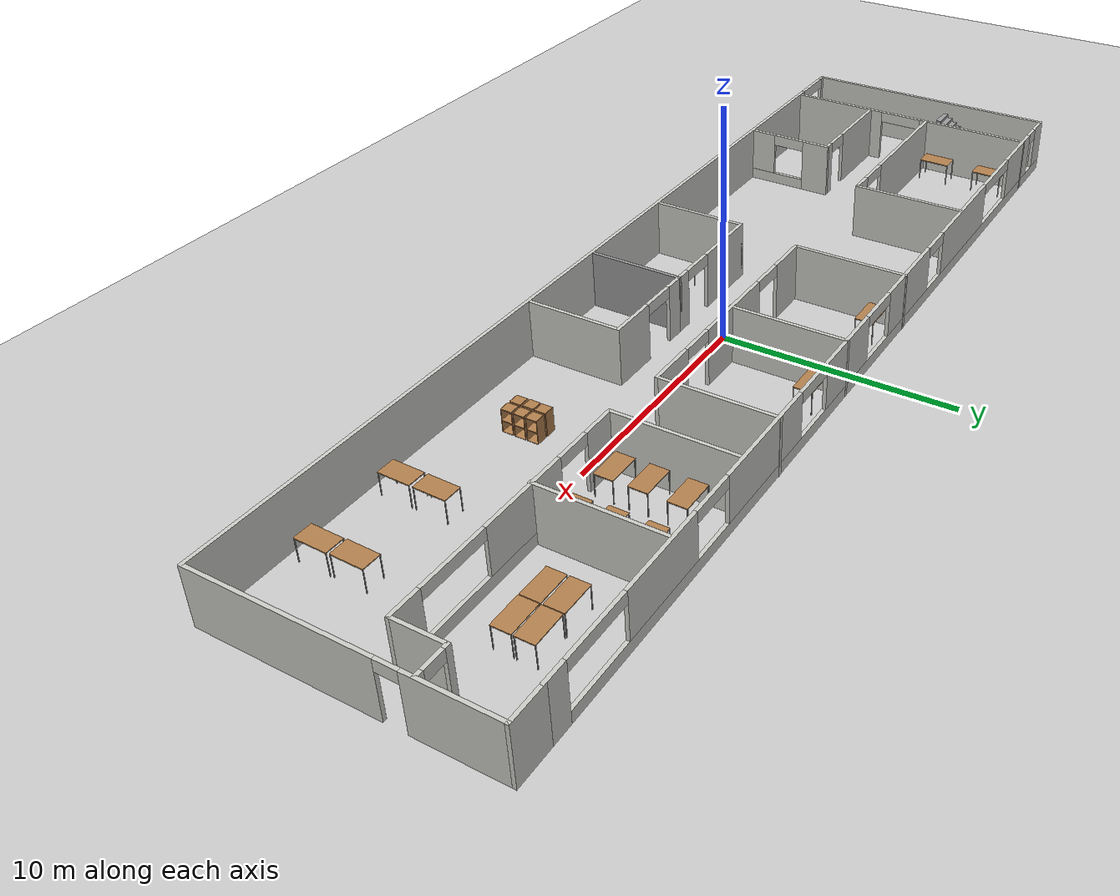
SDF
<sdf version="1.6">
 <world name="default">
  <light name="sun" type="directional">
   <pose>0 0 10 0 -0 0</pose>
   <diffuse>0.8 0.8 0.8 1</diffuse>
   <specular>0.1 0.1 0.1 1</specular>
   <attenuation>
    <range>1000</range>
    <constant>0.9</constant>
    <linear>0.01</linear>
    <quadratic>0.001</quadratic>
   </attenuation>
   <direction>-0.5 0.5 -1</direction>
  </light>
  <model name="ground_plane">
   <static>1</static>
   <link name="link">
    <collision name="collision">
     <geometry><plane><normal>0 0 1</normal><size>100 100</size></plane></geometry>
     <surface><friction><ode><mu>100</mu><mu2>50</mu2></ode></friction></surface>
    </collision>
    <visual name="visual">
     <cast_shadows>0</cast_shadows>
     <geometry><plane><normal>0 0 1</normal><size>100 100</size></plane></geometry>
     <material>
      <script><uri>file://media/materials/scripts/gazebo.material</uri><name>Gazebo/Grey</name></script>
     </material>
    </visual>
   </link>
  </model>
  <gravity>0 0 -9.8</gravity>
  <magnetic_field>6e-06 2.3e-05 -4.2e-05</magnetic_field>
  <atmosphere type="adiabatic"/>
  <physics name="default_physics" default="0" type="ode">
   <max_step_size>0.001</max_step_size>
   <real_time_factor>1</real_time_factor>
   <real_time_update_rate>1000</real_time_update_rate>
  </physics>
  <scene><ambient>0.4 0.4 0.4 1</ambient><background>0.7 0.7 0.7 1</background><shadows>1</shadows></scene>
  <spherical_coordinates>
   <surface_model>EARTH_WGS84</surface_model>
   <latitude_deg>0</latitude_deg>
   <longitude_deg>0</longitude_deg>
   <elevation>0</elevation>
   <heading_deg>0</heading_deg>
  </spherical_coordinates>
  <model name="match_7">
   <pose>0.21975 -0.0084 0 0 -0 0</pose>
   <link name="Stairs_0">
    <visual name="Stairs_0_Visual_0">
     <pose>-19.5832 4.79108 0.083333 0 -0 0</pose>
     <geometry><box><size>1 0.233333 0.166667</size></box></geometry>
     <material>
      <script><uri>file://media/materials/scripts/gazebo.material</uri><name>Gazebo/Grey</name></script>
      <ambient>0.701961 0.717647 0.721569 1</ambient>
     </material>
    </visual>
    <collision name="Stairs_0_Collision_0">
     <geometry><box><size>1 0.233333 0.166667</size></box></geometry>
     <pose>-19.5832 4.79108 0.083333 0 -0 0</pose>
    </collision>
    <visual name="Stairs_0_Visual_1">
     <pose>-19.5832 4.55774 0.25 0 -0 0</pose>
     <geometry><box><size>1 0.233333 0.166667</size></box></geometry>
     <material>
      <script><uri>file://media/materials/scripts/gazebo.material</uri><name>Gazebo/Grey</name></script>
      <ambient>0.701961 0.717647 0.721569 1</ambient>
     </material>
    </visual>
    <collision name="Stairs_0_Collision_1">
     <geometry><box><size>1 0.233333 0.166667</size></box></geometry>
     <pose>-19.5832 4.55774 0.25 0 -0 0</pose>
    </collision>
    <visual name="Stairs_0_Visual_2">
     <pose>-19.5832 4.32441 0.416667 0 -0 0</pose>
     <geometry><box><size>1 0.233333 0.166667</size></box></geometry>
     <material>
      <script><uri>file://media/materials/scripts/gazebo.material</uri><name>Gazebo/Grey</name></script>
      <ambient>0.701961 0.717647 0.721569 1</ambient>
     </material>
    </visual>
    <collision name="Stairs_0_Collision_2">
     <geometry><box><size>1 0.233333 0.166667</size></box></geometry>
     <pose>-19.5832 4.32441 0.416667 0 -0 0</pose>
    </collision>
    <visual name="Stairs_0_Visual_3">
     <pose>-19.5832 4.09108 0.583333 0 -0 0</pose>
     <geometry><box><size>1 0.233333 0.166667</size></box></geometry>
     <material>
      <script><uri>file://media/materials/scripts/gazebo.material</uri><name>Gazebo/Grey</name></script>
      <ambient>0.701961 0.717647 0.721569 1</ambient>
     </material>
    </visual>
    <collision name="Stairs_0_Collision_3">
     <geometry><box><size>1 0.233333 0.166667</size></box></geometry>
     <pose>-19.5832 4.09108 0.583333 0 -0 0</pose>
    </collision>
    <visual name="Stairs_0_Visual_4">
     <pose>-19.5832 3.85774 0.75 0 -0 0</pose>
     <geometry><box><size>1 0.233333 0.166667</size></box></geometry>
     <material>
      <script><uri>file://media/materials/scripts/gazebo.material</uri><name>Gazebo/Grey</name></script>
      <ambient>0.701961 0.717647 0.721569 1</ambient>
     </material>
    </visual>
    <collision name="Stairs_0_Collision_4">
     <geometry><box><size>1 0.233333 0.166667</size></box></geometry>
     <pose>-19.5832 3.85774 0.75 0 -0 0</pose>
    </collision>
    <visual name="Stairs_0_Visual_5">
     <pose>-19.5832 3.62441 0.916667 0 -0 0</pose>
     <geometry><box><size>1 0.233333 0.166667</size></box></geometry>
     <material>
      <script><uri>file://media/materials/scripts/gazebo.material</uri><name>Gazebo/Grey</name></script>
      <ambient>0.701961 0.717647 0.721569 1</ambient>
     </material>
    </visual>
    <collision name="Stairs_0_Collision_5">
     <geometry><box><size>1 0.233333 0.166667</size></box></geometry>
     <pose>-19.5832 3.62441 0.916667 0 -0 0</pose>
    </collision>
    <visual name="Stairs_0_Visual_6">
     <pose>-19.5832 3.39108 1.08333 0 -0 0</pose>
     <geometry><box><size>1 0.233333 0.166667</size></box></geometry>
     <material>
      <script><uri>file://media/materials/scripts/gazebo.material</uri><name>Gazebo/Grey</name></script>
      <ambient>0.701961 0.717647 0.721569 1</ambient>
     </material>
    </visual>
    <collision name="Stairs_0_Collision_6">
     <geometry><box><size>1 0.233333 0.166667</size></box></geometry>
     <pose>-19.5832 3.39108 1.08333 0 -0 0</pose>
    </collision>
    <visual name="Stairs_0_Visual_7">
     <pose>-19.5832 3.15774 1.25 0 -0 0</pose>
     <geometry><box><size>1 0.233333 0.166667</size></box></geometry>
     <material>
      <script><uri>file://media/materials/scripts/gazebo.material</uri><name>Gazebo/Grey</name></script>
      <ambient>0.701961 0.717647 0.721569 1</ambient>
     </material>
    </visual>
    <collision name="Stairs_0_Collision_7">
     <geometry><box><size>1 0.233333 0.166667</size></box></geometry>
     <pose>-19.5832 3.15774 1.25 0 -0 0</pose>
    </collision>
    <visual name="Stairs_0_Visual_8">
     <pose>-19.5832 2.92441 1.41667 0 -0 0</pose>
     <geometry><box><size>1 0.233333 0.166667</size></box></geometry>
     <material>
      <script><uri>file://media/materials/scripts/gazebo.material</uri><name>Gazebo/Grey</name></script>
      <ambient>0.701961 0.717647 0.721569 1</ambient>
     </material>
    </visual>
    <collision name="Stairs_0_Collision_8">
     <geometry><box><size>1 0.233333 0.166667</size></box></geometry>
     <pose>-19.5832 2.92441 1.41667 0 -0 0</pose>
    </collision>
    <visual name="Stairs_0_Visual_9">
     <pose>-19.5832 2.69108 1.58333 0 -0 0</pose>
     <geometry><box><size>1 0.233333 0.166667</size></box></geometry>
     <material>
      <script><uri>file://media/materials/scripts/gazebo.material</uri><name>Gazebo/Grey</name></script>
      <ambient>0.701961 0.717647 0.721569 1</ambient>
     </material>
    </visual>
    <collision name="Stairs_0_Collision_9">
     <geometry><box><size>1 0.233333 0.166667</size></box></geometry>
     <pose>-19.5832 2.69108 1.58333 0 -0 0</pose>
    </collision>
    <visual name="Stairs_0_Visual_10">
     <pose>-19.5832 2.45774 1.75 0 -0 0</pose>
     <geometry><box><size>1 0.233333 0.166667</size></box></geometry>
     <material>
      <script><uri>file://media/materials/scripts/gazebo.material</uri><name>Gazebo/Grey</name></script>
      <ambient>0.701961 0.717647 0.721569 1</ambient>
     </material>
    </visual>
    <collision name="Stairs_0_Collision_10">
     <geometry><box><size>1 0.233333 0.166667</size></box></geometry>
     <pose>-19.5832 2.45774 1.75 0 -0 0</pose>
    </collision>
    <visual name="Stairs_0_Visual_11">
     <pose>-19.5832 2.22441 1.91667 0 -0 0</pose>
     <geometry><box><size>1 0.233333 0.166667</size></box></geometry>
     <material>
      <script><uri>file://media/materials/scripts/gazebo.material</uri><name>Gazebo/Grey</name></script>
      <ambient>0.701961 0.717647 0.721569 1</ambient>
     </material>
    </visual>
    <collision name="Stairs_0_Collision_11">
     <geometry><box><size>1 0.233333 0.166667</size></box></geometry>
     <pose>-19.5832 2.22441 1.91667 0 -0 0</pose>
    </collision>
    <visual name="Stairs_0_Visual_12">
     <pose>-19.5832 1.99108 2.08333 0 -0 0</pose>
     <geometry><box><size>1 0.233333 0.166667</size></box></geometry>
     <material>
      <script><uri>file://media/materials/scripts/gazebo.material</uri><name>Gazebo/Grey</name></script>
      <ambient>0.701961 0.717647 0.721569 1</ambient>
     </material>
    </visual>
    <collision name="Stairs_0_Collision_12">
     <geometry><box><size>1 0.233333 0.166667</size></box></geometry>
     <pose>-19.5832 1.99108 2.08333 0 -0 0</pose>
    </collision>
    <visual name="Stairs_0_Visual_13">
     <pose>-19.5832 1.75774 2.25 0 -0 0</pose>
     <geometry><box><size>1 0.233333 0.166667</size></box></geometry>
     <material>
      <script><uri>file://media/materials/scripts/gazebo.material</uri><name>Gazebo/Grey</name></script>
      <ambient>0.701961 0.717647 0.721569 1</ambient>
     </material>
    </visual>
    <collision name="Stairs_0_Collision_13">
     <geometry><box><size>1 0.233333 0.166667</size></box></geometry>
     <pose>-19.5832 1.75774 2.25 0 -0 0</pose>
    </collision>
    <visual name="Stairs_0_Visual_14">
     <pose>-19.5832 1.52441 2.41667 0 -0 0</pose>
     <geometry><box><size>1 0.233333 0.166667</size></box></geometry>
     <material>
      <script><uri>file://media/materials/scripts/gazebo.material</uri><name>Gazebo/Grey</name></script>
      <ambient>0.701961 0.717647 0.721569 1</ambient>
     </material>
    </visual>
    <collision name="Stairs_0_Collision_14">
     <geometry><box><size>1 0.233333 0.166667</size></box></geometry>
     <pose>-19.5832 1.52441 2.41667 0 -0 0</pose>
    </collision>
   </link>
   <link name="Wall_1">
    <pose>-0.75 5.91533 0 0 -0 3.14159</pose>
    <visual name="Wall_1_Visual_0">
     <pose>-20.2308 0 1.25 0 -0 0</pose>
     <geometry><box><size>1.03842 0.15 2.5</size></box></geometry>
     <material>
      <script><uri>file://media/materials/scripts/gazebo.material</uri><name>Gazebo/CeilingTiled</name></script>
      <ambient>1 1 1 1</ambient>
     </material>
    </visual>
    <collision name="Wall_1_Collision_0">
     <geometry><box><size>1.03842 0.15 2.5</size></box></geometry>
     <pose>-20.2308 0 1.25 0 -0 0</pose>
    </collision>
    <visual name="Wall_1_Visual_1">
     <pose>0.519211 0 0.25 0 -0 0</pose>
     <geometry><box><size>40.4616 0.15 0.5</size></box></geometry>
     <material>
      <script><uri>file://media/materials/scripts/gazebo.material</uri><name>Gazebo/CeilingTiled</name></script>
      <ambient>1 1 1 1</ambient>
     </material>
    </visual>
    <collision name="Wall_1_Collision_1">
     <geometry><box><size>40.4616 0.15 0.5</size></box></geometry>
     <pose>0.519211 0 0.25 0 -0 0</pose>
    </collision>
    <visual name="Wall_1_Visual_2">
     <pose>-14.7343 0 1.5 0 -0 0</pose>
     <geometry><box><size>3.95454 0.15 2</size></box></geometry>
     <material>
      <script><uri>file://media/materials/scripts/gazebo.material</uri><name>Gazebo/CeilingTiled</name></script>
      <ambient>1 1 1 1</ambient>
     </material>
    </visual>
    <collision name="Wall_1_Collision_2">
     <geometry><box><size>3.95454 0.15 2</size></box></geometry>
     <pose>-14.7343 0 1.5 0 -0 0</pose>
    </collision>
    <visual name="Wall_1_Visual_3">
     <pose>-8.16269 0 1.5 0 -0 0</pose>
     <geometry><box><size>5.1887 0.15 2</size></box></geometry>
     <material>
      <script><uri>file://media/materials/scripts/gazebo.material</uri><name>Gazebo/CeilingTiled</name></script>
      <ambient>1 1 1 1</ambient>
     </material>
    </visual>
    <collision name="Wall_1_Collision_3">
     <geometry><box><size>5.1887 0.15 2</size></box></geometry>
     <pose>-8.16269 0 1.5 0 -0 0</pose>
    </collision>
    <visual name="Wall_1_Visual_4">
     <pose>-1.74639 0 1.5 0 -0 0</pose>
     <geometry><box><size>3.6439 0.15 2</size></box></geometry>
     <material>
      <script><uri>file://media/materials/scripts/gazebo.material</uri><name>Gazebo/CeilingTiled</name></script>
      <ambient>1 1 1 1</ambient>
     </material>
    </visual>
    <collision name="Wall_1_Collision_4">
     <geometry><box><size>3.6439 0.15 2</size></box></geometry>
     <pose>-1.74639 0 1.5 0 -0 0</pose>
    </collision>
    <visual name="Wall_1_Visual_5">
     <pose>4.11915 0 1.5 0 -0 0</pose>
     <geometry><box><size>4.08719 0.15 2</size></box></geometry>
     <material>
      <script><uri>file://media/materials/scripts/gazebo.material</uri><name>Gazebo/CeilingTiled</name></script>
      <ambient>1 1 1 1</ambient>
     </material>
    </visual>
    <collision name="Wall_1_Collision_5">
     <geometry><box><size>4.08719 0.15 2</size></box></geometry>
     <pose>4.11915 0 1.5 0 -0 0</pose>
    </collision>
    <visual name="Wall_1_Visual_6">
     <pose>10.219 0 1.5 0 -0 0</pose>
     <geometry><box><size>5.1125 0.15 2</size></box></geometry>
     <material>
      <script><uri>file://media/materials/scripts/gazebo.material</uri><name>Gazebo/CeilingTiled</name></script>
      <ambient>1 1 1 1</ambient>
     </material>
    </visual>
    <collision name="Wall_1_Collision_6">
     <geometry><box><size>5.1125 0.15 2</size></box></geometry>
     <pose>10.219 0 1.5 0 -0 0</pose>
    </collision>
    <visual name="Wall_1_Visual_7">
     <pose>17.3336 0 1.5 0 -0 0</pose>
     <geometry><box><size>3.1168 0.15 2</size></box></geometry>
     <material>
      <script><uri>file://media/materials/scripts/gazebo.material</uri><name>Gazebo/CeilingTiled</name></script>
      <ambient>1 1 1 1</ambient>
     </material>
    </visual>
    <collision name="Wall_1_Collision_7">
     <geometry><box><size>3.1168 0.15 2</size></box></geometry>
     <pose>17.3336 0 1.5 0 -0 0</pose>
    </collision>
    <visual name="Wall_1_Visual_8">
     <pose>20.221 0 1.5 0 -0 0</pose>
     <geometry><box><size>1.05796 0.15 2</size></box></geometry>
     <material>
      <script><uri>file://media/materials/scripts/gazebo.material</uri><name>Gazebo/CeilingTiled</name></script>
      <ambient>1 1 1 1</ambient>
     </material>
    </visual>
    <collision name="Wall_1_Collision_8">
     <geometry><box><size>1.05796 0.15 2</size></box></geometry>
     <pose>20.221 0 1.5 0 -0 0</pose>
    </collision>
    <visual name="Wall_1_Visual_9">
     <pose>-18.2116 0 2.25 0 -0 0</pose>
     <geometry><box><size>3 0.15 0.5</size></box></geometry>
     <material>
      <script><uri>file://media/materials/scripts/gazebo.material</uri><name>Gazebo/CeilingTiled</name></script>
      <ambient>1 1 1 1</ambient>
     </material>
    </visual>
    <collision name="Wall_1_Collision_9">
     <geometry><box><size>3 0.15 0.5</size></box></geometry>
     <pose>-18.2116 0 2.25 0 -0 0</pose>
    </collision>
    <visual name="Wall_1_Visual_10">
     <pose>-11.757 0 2.25 0 -0 0</pose>
     <geometry><box><size>2 0.15 0.5</size></box></geometry>
     <material>
      <script><uri>file://media/materials/scripts/gazebo.material</uri><name>Gazebo/CeilingTiled</name></script>
      <ambient>1 1 1 1</ambient>
     </material>
    </visual>
    <collision name="Wall_1_Collision_10">
     <geometry><box><size>2 0.15 0.5</size></box></geometry>
     <pose>-11.757 0 2.25 0 -0 0</pose>
    </collision>
    <visual name="Wall_1_Visual_11">
     <pose>-4.56834 0 2.25 0 -0 0</pose>
     <geometry><box><size>2 0.15 0.5</size></box></geometry>
     <material>
      <script><uri>file://media/materials/scripts/gazebo.material</uri><name>Gazebo/CeilingTiled</name></script>
      <ambient>1 1 1 1</ambient>
     </material>
    </visual>
    <collision name="Wall_1_Collision_11">
     <geometry><box><size>2 0.15 0.5</size></box></geometry>
     <pose>-4.56834 0 2.25 0 -0 0</pose>
    </collision>
    <visual name="Wall_1_Visual_12">
     <pose>1.07556 0 2.25 0 -0 0</pose>
     <geometry><box><size>2 0.15 0.5</size></box></geometry>
     <material>
      <script><uri>file://media/materials/scripts/gazebo.material</uri><name>Gazebo/CeilingTiled</name></script>
      <ambient>1 1 1 1</ambient>
     </material>
    </visual>
    <collision name="Wall_1_Collision_12">
     <geometry><box><size>2 0.15 0.5</size></box></geometry>
     <pose>1.07556 0 2.25 0 -0 0</pose>
    </collision>
    <visual name="Wall_1_Visual_13">
     <pose>6.91275 0 2.25 0 -0 0</pose>
     <geometry><box><size>1.5 0.15 0.5</size></box></geometry>
     <material>
      <script><uri>file://media/materials/scripts/gazebo.material</uri><name>Gazebo/CeilingTiled</name></script>
      <ambient>1 1 1 1</ambient>
     </material>
    </visual>
    <collision name="Wall_1_Collision_13">
     <geometry><box><size>1.5 0.15 0.5</size></box></geometry>
     <pose>6.91275 0 2.25 0 -0 0</pose>
    </collision>
    <visual name="Wall_1_Visual_14">
     <pose>14.2752 0 2.25 0 -0 0</pose>
     <geometry><box><size>3 0.15 0.5</size></box></geometry>
     <material>
      <script><uri>file://media/materials/scripts/gazebo.material</uri><name>Gazebo/CeilingTiled</name></script>
      <ambient>1 1 1 1</ambient>
     </material>
    </visual>
    <collision name="Wall_1_Collision_14">
     <geometry><box><size>3 0.15 0.5</size></box></geometry>
     <pose>14.2752 0 2.25 0 -0 0</pose>
    </collision>
    <visual name="Wall_1_Visual_15">
     <pose>19.292 0 2.25 0 -0 0</pose>
     <geometry><box><size>0.8 0.15 0.5</size></box></geometry>
     <material>
      <script><uri>file://media/materials/scripts/gazebo.material</uri><name>Gazebo/CeilingTiled</name></script>
      <ambient>1 1 1 1</ambient>
     </material>
    </visual>
    <collision name="Wall_1_Collision_15">
     <geometry><box><size>0.8 0.15 0.5</size></box></geometry>
     <pose>19.292 0 2.25 0 -0 0</pose>
    </collision>
   </link>
   <link name="Wall_10">
    <collision name="Wall_10_Collision">
     <geometry><box><size>5.25 0.15 2.5</size></box></geometry>
     <pose>0 0 1.25 0 -0 0</pose>
    </collision>
    <visual name="Wall_10_Visual">
     <pose>0 0 1.25 0 -0 0</pose>
     <geometry><box><size>5.25 0.15 2.5</size></box></geometry>
     <material>
      <script><uri>file://media/materials/scripts/gazebo.material</uri><name>Gazebo/CeilingTiled</name></script>
      <ambient>1 1 1 1</ambient>
     </material>
    </visual>
    <pose>8.9562 3.2768 0 0 -0 1.5708</pose>
   </link>
   <link name="Wall_12">
    <collision name="Wall_12_Collision">
     <geometry><box><size>5 0.15 2.5</size></box></geometry>
     <pose>0 0 1.25 0 -0 0</pose>
    </collision>
    <visual name="Wall_12_Visual">
     <pose>0 0 1.25 0 -0 0</pose>
     <geometry><box><size>5 0.15 2.5</size></box></geometry>
     <material>
      <script><uri>file://media/materials/scripts/gazebo.material</uri><name>Gazebo/CeilingTiled</name></script>
      <ambient>1 1 1 1</ambient>
     </material>
    </visual>
    <pose>6.46195 3.50968 0 0 0 -1.5708</pose>
   </link>
   <link name="Wall_13">
    <pose>1.03695 1.08468 0 0 -0 3.14159</pose>
    <visual name="Wall_13_Visual_0">
     <pose>-4.45451 0 1.25 0 -0 0</pose>
     <geometry><box><size>2.09097 0.15 2.5</size></box></geometry>
     <material>
      <script><uri>file://media/materials/scripts/gazebo.material</uri><name>Gazebo/CeilingTiled</name></script>
      <ambient>1 1 1 1</ambient>
     </material>
    </visual>
    <collision name="Wall_13_Collision_0">
     <geometry><box><size>2.09097 0.15 2.5</size></box></geometry>
     <pose>-4.45451 0 1.25 0 -0 0</pose>
    </collision>
    <visual name="Wall_13_Visual_1">
     <pose>0.101743 0 1.25 0 -0 0</pose>
     <geometry><box><size>4.02154 0.15 2.5</size></box></geometry>
     <material>
      <script><uri>file://media/materials/scripts/gazebo.material</uri><name>Gazebo/CeilingTiled</name></script>
      <ambient>1 1 1 1</ambient>
     </material>
    </visual>
    <collision name="Wall_13_Collision_1">
     <geometry><box><size>4.02154 0.15 2.5</size></box></geometry>
     <pose>0.101743 0 1.25 0 -0 0</pose>
    </collision>
    <visual name="Wall_13_Visual_2">
     <pose>4.55626 0 1.25 0 -0 0</pose>
     <geometry><box><size>1.88749 0.15 2.5</size></box></geometry>
     <material>
      <script><uri>file://media/materials/scripts/gazebo.material</uri><name>Gazebo/CeilingTiled</name></script>
      <ambient>1 1 1 1</ambient>
     </material>
    </visual>
    <collision name="Wall_13_Collision_2">
     <geometry><box><size>1.88749 0.15 2.5</size></box></geometry>
     <pose>4.55626 0 1.25 0 -0 0</pose>
    </collision>
    <visual name="Wall_13_Visual_3">
     <pose>-2.65903 0 2.25 0 -0 0</pose>
     <geometry><box><size>1.5 0.15 0.5</size></box></geometry>
     <material>
      <script><uri>file://media/materials/scripts/gazebo.material</uri><name>Gazebo/CeilingTiled</name></script>
      <ambient>1 1 1 1</ambient>
     </material>
    </visual>
    <collision name="Wall_13_Collision_3">
     <geometry><box><size>1.5 0.15 0.5</size></box></geometry>
     <pose>-2.65903 0 2.25 0 -0 0</pose>
    </collision>
    <visual name="Wall_13_Visual_4">
     <pose>2.86251 0 2.25 0 -0 0</pose>
     <geometry><box><size>1.5 0.15 0.5</size></box></geometry>
     <material>
      <script><uri>file://media/materials/scripts/gazebo.material</uri><name>Gazebo/CeilingTiled</name></script>
      <ambient>1 1 1 1</ambient>
     </material>
    </visual>
    <collision name="Wall_13_Collision_4">
     <geometry><box><size>1.5 0.15 0.5</size></box></geometry>
     <pose>2.86251 0 2.25 0 -0 0</pose>
    </collision>
   </link>
   <link name="Wall_14">
    <collision name="Wall_14_Collision">
     <geometry><box><size>5 0.15 2.5</size></box></geometry>
     <pose>0 0 1.25 0 -0 0</pose>
    </collision>
    <visual name="Wall_14_Visual">
     <pose>0 0 1.25 0 -0 0</pose>
     <geometry><box><size>5 0.15 2.5</size></box></geometry>
     <material>
      <script><uri>file://media/materials/scripts/gazebo.material</uri><name>Gazebo/CeilingTiled</name></script>
      <ambient>1 1 1 1</ambient>
     </material>
    </visual>
    <pose>-4.38805 3.50968 0 0 -0 1.5708</pose>
   </link>
   <link name="Wall_16">
    <collision name="Wall_16_Collision">
     <geometry><box><size>5.25 0.15 2.5</size></box></geometry>
     <pose>0 0 1.25 0 -0 0</pose>
    </collision>
    <visual name="Wall_16_Visual">
     <pose>0 0 1.25 0 -0 0</pose>
     <geometry><box><size>5.25 0.15 2.5</size></box></geometry>
     <material>
      <script><uri>file://media/materials/scripts/gazebo.material</uri><name>Gazebo/CeilingTiled</name></script>
      <ambient>1 1 1 1</ambient>
     </material>
    </visual>
    <pose>13.3654 3.23435 0 0 -0 1.5708</pose>
   </link>
   <link name="Wall_18">
    <pose>-18.7767 -0.006144 0 0 -0 1.5708</pose>
    <visual name="Wall_18_Visual_0">
     <pose>-3.6617 0 1.25 0 -0 0</pose>
     <geometry><box><size>4.6766 0.15 2.5</size></box></geometry>
     <material>
      <script><uri>file://media/materials/scripts/gazebo.material</uri><name>Gazebo/CeilingTiled</name></script>
      <ambient>1 1 1 1</ambient>
     </material>
    </visual>
    <collision name="Wall_18_Collision_0">
     <geometry><box><size>4.6766 0.15 2.5</size></box></geometry>
     <pose>-3.6617 0 1.25 0 -0 0</pose>
    </collision>
    <visual name="Wall_18_Visual_1">
     <pose>3.3383 0 1.25 0 -0 0</pose>
     <geometry><box><size>5.3234 0.15 2.5</size></box></geometry>
     <material>
      <script><uri>file://media/materials/scripts/gazebo.material</uri><name>Gazebo/CeilingTiled</name></script>
      <ambient>1 1 1 1</ambient>
     </material>
    </visual>
    <collision name="Wall_18_Collision_1">
     <geometry><box><size>5.3234 0.15 2.5</size></box></geometry>
     <pose>3.3383 0 1.25 0 -0 0</pose>
    </collision>
    <visual name="Wall_18_Visual_2">
     <pose>-0.323398 0 2.25 0 -0 0</pose>
     <geometry><box><size>2 0.15 0.5</size></box></geometry>
     <material>
      <script><uri>file://media/materials/scripts/gazebo.material</uri><name>Gazebo/CeilingTiled</name></script>
      <ambient>1 1 1 1</ambient>
     </material>
    </visual>
    <collision name="Wall_18_Collision_2">
     <geometry><box><size>2 0.15 0.5</size></box></geometry>
     <pose>-0.323398 0 2.25 0 -0 0</pose>
    </collision>
   </link>
   <link name="Wall_2">
    <collision name="Wall_2_Collision">
     <geometry><box><size>12 0.15 2.5</size></box></geometry>
     <pose>0 0 1.25 0 -0 0</pose>
    </collision>
    <visual name="Wall_2_Visual">
     <pose>0 0 1.25 0 -0 0</pose>
     <geometry><box><size>12 0.15 2.5</size></box></geometry>
     <material>
      <script><uri>file://media/materials/scripts/gazebo.material</uri><name>Gazebo/CeilingTiled</name></script>
      <ambient>1 1 1 1</ambient>
     </material>
    </visual>
    <pose>-21.425 -0.009675 0 0 0 -1.5708</pose>
   </link>
   <link name="Wall_21">
    <pose>-14.7152 1.00336 0 0 -0 0</pose>
    <visual name="Wall_21_Visual_0">
     <pose>-1.26951 0 1.25 0 -0 0</pose>
     <geometry><box><size>5.71098 0.15 2.5</size></box></geometry>
     <material>
      <script><uri>file://media/materials/scripts/gazebo.material</uri><name>Gazebo/CeilingTiled</name></script>
      <ambient>1 1 1 1</ambient>
     </material>
    </visual>
    <collision name="Wall_21_Collision_0">
     <geometry><box><size>5.71098 0.15 2.5</size></box></geometry>
     <pose>-1.26951 0 1.25 0 -0 0</pose>
    </collision>
    <visual name="Wall_21_Visual_1">
     <pose>3.60549 0 1.25 0 -0 0</pose>
     <geometry><box><size>1.03902 0.15 2.5</size></box></geometry>
     <material>
      <script><uri>file://media/materials/scripts/gazebo.material</uri><name>Gazebo/CeilingTiled</name></script>
      <ambient>1 1 1 1</ambient>
     </material>
    </visual>
    <collision name="Wall_21_Collision_1">
     <geometry><box><size>1.03902 0.15 2.5</size></box></geometry>
     <pose>3.60549 0 1.25 0 -0 0</pose>
    </collision>
    <visual name="Wall_21_Visual_2">
     <pose>2.33598 0 2.25 0 -0 0</pose>
     <geometry><box><size>1.5 0.15 0.5</size></box></geometry>
     <material>
      <script><uri>file://media/materials/scripts/gazebo.material</uri><name>Gazebo/CeilingTiled</name></script>
      <ambient>1 1 1 1</ambient>
     </material>
    </visual>
    <collision name="Wall_21_Collision_2">
     <geometry><box><size>1.5 0.15 0.5</size></box></geometry>
     <pose>2.33598 0 2.25 0 -0 0</pose>
    </collision>
   </link>
   <link name="Wall_22">
    <collision name="Wall_22_Collision">
     <geometry><box><size>5 0.15 2.5</size></box></geometry>
     <pose>0 0 1.25 0 -0 0</pose>
    </collision>
    <visual name="Wall_22_Visual">
     <pose>0 0 1.25 0 -0 0</pose>
     <geometry><box><size>5 0.15 2.5</size></box></geometry>
     <material>
      <script><uri>file://media/materials/scripts/gazebo.material</uri><name>Gazebo/CeilingTiled</name></script>
      <ambient>1 1 1 1</ambient>
     </material>
    </visual>
    <pose>-10.6652 3.42836 0 0 -0 1.5708</pose>
   </link>
   <link name="Wall_24">
    <pose>-16.2497 -1.96364 0 0 -0 0</pose>
    <visual name="Wall_24_Visual_0">
     <pose>-0.86263 0 1.25 0 -0 0</pose>
     <geometry><box><size>3.52474 0.15 2.5</size></box></geometry>
     <material>
      <script><uri>file://media/materials/scripts/gazebo.material</uri><name>Gazebo/CeilingTiled</name></script>
      <ambient>1 1 1 1</ambient>
     </material>
    </visual>
    <collision name="Wall_24_Collision_0">
     <geometry><box><size>3.52474 0.15 2.5</size></box></geometry>
     <pose>-0.86263 0 1.25 0 -0 0</pose>
    </collision>
    <visual name="Wall_24_Visual_1">
     <pose>2.36237 0 1.25 0 -0 0</pose>
     <geometry><box><size>0.525259 0.15 2.5</size></box></geometry>
     <material>
      <script><uri>file://media/materials/scripts/gazebo.material</uri><name>Gazebo/CeilingTiled</name></script>
      <ambient>1 1 1 1</ambient>
     </material>
    </visual>
    <collision name="Wall_24_Collision_1">
     <geometry><box><size>0.525259 0.15 2.5</size></box></geometry>
     <pose>2.36237 0 1.25 0 -0 0</pose>
    </collision>
    <visual name="Wall_24_Visual_2">
     <pose>1.49974 0 2.25 0 -0 0</pose>
     <geometry><box><size>1.2 0.15 0.5</size></box></geometry>
     <material>
      <script><uri>file://media/materials/scripts/gazebo.material</uri><name>Gazebo/CeilingTiled</name></script>
      <ambient>1 1 1 1</ambient>
     </material>
    </visual>
    <collision name="Wall_24_Collision_2">
     <geometry><box><size>1.2 0.15 0.5</size></box></geometry>
     <pose>1.49974 0 2.25 0 -0 0</pose>
    </collision>
   </link>
   <link name="Wall_25">
    <pose>-13.6997 -3.88864 0 0 0 -1.5708</pose>
    <visual name="Wall_25_Visual_0">
     <pose>-1.34208 0 1.25 0 -0 0</pose>
     <geometry><box><size>1.31584 0.15 2.5</size></box></geometry>
     <material>
      <script><uri>file://media/materials/scripts/gazebo.material</uri><name>Gazebo/CeilingTiled</name></script>
      <ambient>1 1 1 1</ambient>
     </material>
    </visual>
    <collision name="Wall_25_Collision_0">
     <geometry><box><size>1.31584 0.15 2.5</size></box></geometry>
     <pose>-1.34208 0 1.25 0 -0 0</pose>
    </collision>
    <visual name="Wall_25_Visual_1">
     <pose>0.65792 0 0.25 0 -0 0</pose>
     <geometry><box><size>2.68416 0.15 0.5</size></box></geometry>
     <material>
      <script><uri>file://media/materials/scripts/gazebo.material</uri><name>Gazebo/CeilingTiled</name></script>
      <ambient>1 1 1 1</ambient>
     </material>
    </visual>
    <collision name="Wall_25_Collision_1">
     <geometry><box><size>2.68416 0.15 0.5</size></box></geometry>
     <pose>0.65792 0 0.25 0 -0 0</pose>
    </collision>
    <visual name="Wall_25_Visual_2">
     <pose>1.40792 0 1.5 0 -0 0</pose>
     <geometry><box><size>1.18416 0.15 2</size></box></geometry>
     <material>
      <script><uri>file://media/materials/scripts/gazebo.material</uri><name>Gazebo/CeilingTiled</name></script>
      <ambient>1 1 1 1</ambient>
     </material>
    </visual>
    <collision name="Wall_25_Collision_2">
     <geometry><box><size>1.18416 0.15 2</size></box></geometry>
     <pose>1.40792 0 1.5 0 -0 0</pose>
    </collision>
    <visual name="Wall_25_Visual_3">
     <pose>0.06584 0 2.25 0 -0 0</pose>
     <geometry><box><size>1.5 0.15 0.5</size></box></geometry>
     <material>
      <script><uri>file://media/materials/scripts/gazebo.material</uri><name>Gazebo/CeilingTiled</name></script>
      <ambient>1 1 1 1</ambient>
     </material>
    </visual>
    <collision name="Wall_25_Collision_3">
     <geometry><box><size>1.5 0.15 0.5</size></box></geometry>
     <pose>0.06584 0 2.25 0 -0 0</pose>
    </collision>
   </link>
   <link name="Wall_28">
    <collision name="Wall_28_Collision">
     <geometry><box><size>5 0.15 2.5</size></box></geometry>
     <pose>0 0 1.25 0 -0 0</pose>
    </collision>
    <visual name="Wall_28_Visual">
     <pose>0 0 1.25 0 -0 0</pose>
     <geometry><box><size>5 0.15 2.5</size></box></geometry>
     <material>
      <script><uri>file://media/materials/scripts/gazebo.material</uri><name>Gazebo/CeilingTiled</name></script>
      <ambient>1 1 1 1</ambient>
     </material>
    </visual>
    <pose>1.044 3.49253 0 0 -0 1.5708</pose>
   </link>
   <link name="Wall_3">
    <pose>0 -5.93468 0 0 -0 0</pose>
    <visual name="Wall_3_Visual_0">
     <pose>-21.3246 0 1.25 0 -0 0</pose>
     <geometry><box><size>0.350892 0.15 2.5</size></box></geometry>
     <material>
      <script><uri>file://media/materials/scripts/gazebo.material</uri><name>Gazebo/CeilingTiled</name></script>
      <ambient>1 1 1 1</ambient>
     </material>
    </visual>
    <collision name="Wall_3_Collision_0">
     <geometry><box><size>0.350892 0.15 2.5</size></box></geometry>
     <pose>-21.3246 0 1.25 0 -0 0</pose>
    </collision>
    <visual name="Wall_3_Visual_1">
     <pose>1.17545 0 1.25 0 -0 0</pose>
     <geometry><box><size>40.6491 0.15 2.5</size></box></geometry>
     <material>
      <script><uri>file://media/materials/scripts/gazebo.material</uri><name>Gazebo/CeilingTiled</name></script>
      <ambient>1 1 1 1</ambient>
     </material>
    </visual>
    <collision name="Wall_3_Collision_1">
     <geometry><box><size>40.6491 0.15 2.5</size></box></geometry>
     <pose>1.17545 0 1.25 0 -0 0</pose>
    </collision>
    <visual name="Wall_3_Visual_2">
     <pose>-20.1491 0 2.25 0 -0 0</pose>
     <geometry><box><size>2 0.15 0.5</size></box></geometry>
     <material>
      <script><uri>file://media/materials/scripts/gazebo.material</uri><name>Gazebo/CeilingTiled</name></script>
      <ambient>1 1 1 1</ambient>
     </material>
    </visual>
    <collision name="Wall_3_Collision_2">
     <geometry><box><size>2 0.15 0.5</size></box></geometry>
     <pose>-20.1491 0 2.25 0 -0 0</pose>
    </collision>
   </link>
   <link name="Wall_32">
    <collision name="Wall_32_Collision">
     <geometry><box><size>4.25 0.15 2.5</size></box></geometry>
     <pose>0 0 1.25 0 -0 0</pose>
    </collision>
    <visual name="Wall_32_Visual">
     <pose>0 0 1.25 0 -0 0</pose>
     <geometry><box><size>4.25 0.15 2.5</size></box></geometry>
     <material>
      <script><uri>file://media/materials/scripts/gazebo.material</uri><name>Gazebo/CeilingTiled</name></script>
      <ambient>1 1 1 1</ambient>
     </material>
    </visual>
    <pose>-4.91517 -3.84696 0 0 -0 1.5708</pose>
   </link>
   <link name="Wall_33">
    <pose>-2.36517 -1.79696 0 0 -0 0</pose>
    <visual name="Wall_33_Visual_0">
     <pose>-1.11101 0 1.25 0 -0 0</pose>
     <geometry><box><size>3.02797 0.15 2.5</size></box></geometry>
     <material>
      <script><uri>file://media/materials/scripts/gazebo.material</uri><name>Gazebo/CeilingTiled</name></script>
      <ambient>1 1 1 1</ambient>
     </material>
    </visual>
    <collision name="Wall_33_Collision_0">
     <geometry><box><size>3.02797 0.15 2.5</size></box></geometry>
     <pose>-1.11101 0 1.25 0 -0 0</pose>
    </collision>
    <visual name="Wall_33_Visual_1">
     <pose>2.26399 0 1.25 0 -0 0</pose>
     <geometry><box><size>0.722026 0.15 2.5</size></box></geometry>
     <material>
      <script><uri>file://media/materials/scripts/gazebo.material</uri><name>Gazebo/CeilingTiled</name></script>
      <ambient>1 1 1 1</ambient>
     </material>
    </visual>
    <collision name="Wall_33_Collision_1">
     <geometry><box><size>0.722026 0.15 2.5</size></box></geometry>
     <pose>2.26399 0 1.25 0 -0 0</pose>
    </collision>
    <visual name="Wall_33_Visual_2">
     <pose>1.15297 0 2.25 0 -0 0</pose>
     <geometry><box><size>1.5 0.15 0.5</size></box></geometry>
     <material>
      <script><uri>file://media/materials/scripts/gazebo.material</uri><name>Gazebo/CeilingTiled</name></script>
      <ambient>1 1 1 1</ambient>
     </material>
    </visual>
    <collision name="Wall_33_Collision_2">
     <geometry><box><size>1.5 0.15 0.5</size></box></geometry>
     <pose>1.15297 0 2.25 0 -0 0</pose>
    </collision>
   </link>
   <link name="Wall_34">
    <collision name="Wall_34_Collision">
     <geometry><box><size>4.25 0.15 2.5</size></box></geometry>
     <pose>0 0 1.25 0 -0 0</pose>
    </collision>
    <visual name="Wall_34_Visual">
     <pose>0 0 1.25 0 -0 0</pose>
     <geometry><box><size>4.25 0.15 2.5</size></box></geometry>
     <material>
      <script><uri>file://media/materials/scripts/gazebo.material</uri><name>Gazebo/Grey</name></script>
      <ambient>1 1 1 1</ambient>
     </material>
    </visual>
    <pose>0.184826 -3.84696 0 0 0 -1.5708</pose>
   </link>
   <link name="Wall_36">
    <pose>2.35983 -1.79696 0 0 -0 0</pose>
    <visual name="Wall_36_Visual_0">
     <pose>-1.78975 0 1.25 0 -0 0</pose>
     <geometry><box><size>0.920497 0.15 2.5</size></box></geometry>
     <material>
      <script><uri>file://media/materials/scripts/gazebo.material</uri><name>Gazebo/CeilingTiled</name></script>
      <ambient>1 1 1 1</ambient>
     </material>
    </visual>
    <collision name="Wall_36_Collision_0">
     <geometry><box><size>0.920497 0.15 2.5</size></box></geometry>
     <pose>-1.78975 0 1.25 0 -0 0</pose>
    </collision>
    <visual name="Wall_36_Visual_1">
     <pose>1.21025 0 1.25 0 -0 0</pose>
     <geometry><box><size>2.0795 0.15 2.5</size></box></geometry>
     <material>
      <script><uri>file://media/materials/scripts/gazebo.material</uri><name>Gazebo/CeilingTiled</name></script>
      <ambient>1 1 1 1</ambient>
     </material>
    </visual>
    <collision name="Wall_36_Collision_1">
     <geometry><box><size>2.0795 0.15 2.5</size></box></geometry>
     <pose>1.21025 0 1.25 0 -0 0</pose>
    </collision>
    <visual name="Wall_36_Visual_2">
     <pose>-0.579503 0 2.25 0 -0 0</pose>
     <geometry><box><size>1.5 0.15 0.5</size></box></geometry>
     <material>
      <script><uri>file://media/materials/scripts/gazebo.material</uri><name>Gazebo/CeilingTiled</name></script>
      <ambient>1 1 1 1</ambient>
     </material>
    </visual>
    <collision name="Wall_36_Collision_2">
     <geometry><box><size>1.5 0.15 0.5</size></box></geometry>
     <pose>-0.579503 0 2.25 0 -0 0</pose>
    </collision>
   </link>
   <link name="Wall_37">
    <collision name="Wall_37_Collision">
     <geometry><box><size>4.25 0.15 2.5</size></box></geometry>
     <pose>0 0 1.25 0 -0 0</pose>
    </collision>
    <visual name="Wall_37_Visual">
     <pose>0 0 1.25 0 -0 0</pose>
     <geometry><box><size>4.25 0.15 2.5</size></box></geometry>
     <material>
      <script><uri>file://media/materials/scripts/gazebo.material</uri><name>Gazebo/CeilingTiled</name></script>
      <ambient>1 1 1 1</ambient>
     </material>
    </visual>
    <pose>4.53483 -3.84696 0 0 0 -1.5708</pose>
   </link>
   <link name="Wall_4">
    <pose>21.425 -0.009675 0 0 -0 1.5708</pose>
    <visual name="Wall_4_Visual_0">
     <pose>-2.29898 0 1.25 0 -0 0</pose>
     <geometry><box><size>7.40204 0.15 2.5</size></box></geometry>
     <material>
      <script><uri>file://media/materials/scripts/gazebo.material</uri><name>Gazebo/CeilingTiled</name></script>
      <ambient>1 1 1 1</ambient>
     </material>
    </visual>
    <collision name="Wall_4_Collision_0">
     <geometry><box><size>7.40204 0.15 2.5</size></box></geometry>
     <pose>-2.29898 0 1.25 0 -0 0</pose>
    </collision>
    <visual name="Wall_4_Visual_1">
     <pose>4.15102 0 1.25 0 -0 0</pose>
     <geometry><box><size>3.69796 0.15 2.5</size></box></geometry>
     <material>
      <script><uri>file://media/materials/scripts/gazebo.material</uri><name>Gazebo/CeilingTiled</name></script>
      <ambient>1 1 1 1</ambient>
     </material>
    </visual>
    <collision name="Wall_4_Collision_1">
     <geometry><box><size>3.69796 0.15 2.5</size></box></geometry>
     <pose>4.15102 0 1.25 0 -0 0</pose>
    </collision>
    <visual name="Wall_4_Visual_2">
     <pose>1.85204 0 2.25 0 -0 0</pose>
     <geometry><box><size>0.9 0.15 0.5</size></box></geometry>
     <material>
      <script><uri>file://media/materials/scripts/gazebo.material</uri><name>Gazebo/CeilingTiled</name></script>
      <ambient>1 1 1 1</ambient>
     </material>
    </visual>
    <collision name="Wall_4_Collision_2">
     <geometry><box><size>0.9 0.15 0.5</size></box></geometry>
     <pose>1.85204 0 2.25 0 -0 0</pose>
    </collision>
   </link>
   <link name="Wall_5">
    <collision name="Wall_5_Collision">
     <geometry><box><size>1.65 0.15 2.5</size></box></geometry>
     <pose>0 0 1.25 0 -0 0</pose>
    </collision>
    <visual name="Wall_5_Visual">
     <pose>0 0 1.25 0 -0 0</pose>
     <geometry><box><size>1.65 0.15 2.5</size></box></geometry>
     <material>
      <script><uri>file://media/materials/scripts/gazebo.material</uri><name>Gazebo/CeilingTiled</name></script>
      <ambient>1 1 1 1</ambient>
     </material>
    </visual>
    <pose>20.675 5.91533 0 0 0 -3.14159</pose>
   </link>
   <link name="Wall_7">
    <pose>20.7312 2.8268 0 0 -0 3.14159</pose>
    <visual name="Wall_7_Visual_0">
     <pose>-0.578824 0 1.25 0 -0 0</pose>
     <geometry><box><size>0.342353 0.15 2.5</size></box></geometry>
     <material>
      <script><uri>file://media/materials/scripts/gazebo.material</uri><name>Gazebo/CeilingTiled</name></script>
      <ambient>1 1 1 1</ambient>
     </material>
    </visual>
    <collision name="Wall_7_Collision_0">
     <geometry><box><size>0.342353 0.15 2.5</size></box></geometry>
     <pose>-0.578824 0 1.25 0 -0 0</pose>
    </collision>
    <visual name="Wall_7_Visual_1">
     <pose>0.621176 0 1.25 0 -0 0</pose>
     <geometry><box><size>0.257647 0.15 2.5</size></box></geometry>
     <material>
      <script><uri>file://media/materials/scripts/gazebo.material</uri><name>Gazebo/CeilingTiled</name></script>
      <ambient>1 1 1 1</ambient>
     </material>
    </visual>
    <collision name="Wall_7_Collision_1">
     <geometry><box><size>0.257647 0.15 2.5</size></box></geometry>
     <pose>0.621176 0 1.25 0 -0 0</pose>
    </collision>
    <visual name="Wall_7_Visual_2">
     <pose>0.042353 0 2.25 0 -0 0</pose>
     <geometry><box><size>0.9 0.15 0.5</size></box></geometry>
     <material>
      <script><uri>file://media/materials/scripts/gazebo.material</uri><name>Gazebo/CeilingTiled</name></script>
      <ambient>1 1 1 1</ambient>
     </material>
    </visual>
    <collision name="Wall_7_Collision_2">
     <geometry><box><size>0.9 0.15 0.5</size></box></geometry>
     <pose>0.042353 0 2.25 0 -0 0</pose>
    </collision>
   </link>
   <link name="Wall_8">
    <collision name="Wall_8_Collision">
     <geometry><box><size>2.25 0.15 2.5</size></box></geometry>
     <pose>0 0 1.25 0 -0 0</pose>
    </collision>
    <visual name="Wall_8_Visual">
     <pose>0 0 1.25 0 -0 0</pose>
     <geometry><box><size>2.25 0.15 2.5</size></box></geometry>
     <material>
      <script><uri>file://media/materials/scripts/gazebo.material</uri><name>Gazebo/CeilingTiled</name></script>
      <ambient>1 1 1 1</ambient>
     </material>
    </visual>
    <pose>20.0562 1.7768 0 0 0 -1.5708</pose>
   </link>
   <link name="Wall_9">
    <pose>14.5062 0.7268 0 0 -0 3.14159</pose>
    <visual name="Wall_9_Visual_0">
     <pose>-4.94842 0 1.25 0 -0 0</pose>
     <geometry><box><size>1.35316 0.15 2.5</size></box></geometry>
     <material>
      <script><uri>file://media/materials/scripts/gazebo.material</uri><name>Gazebo/CeilingTiled</name></script>
      <ambient>1 1 1 1</ambient>
     </material>
    </visual>
    <collision name="Wall_9_Collision_0">
     <geometry><box><size>1.35316 0.15 2.5</size></box></geometry>
     <pose>-4.94842 0 1.25 0 -0 0</pose>
    </collision>
    <visual name="Wall_9_Visual_1">
     <pose>4.86825 0 1.25 0 -0 0</pose>
     <geometry><box><size>1.5135 0.15 2.5</size></box></geometry>
     <material>
      <script><uri>file://media/materials/scripts/gazebo.material</uri><name>Gazebo/CeilingTiled</name></script>
      <ambient>1 1 1 1</ambient>
     </material>
    </visual>
    <collision name="Wall_9_Collision_1">
     <geometry><box><size>1.5135 0.15 2.5</size></box></geometry>
     <pose>4.86825 0 1.25 0 -0 0</pose>
    </collision>
    <visual name="Wall_9_Visual_2">
     <pose>-0.830167 0 0.25 0 -0 0</pose>
     <geometry><box><size>6.88334 0.15 0.5</size></box></geometry>
     <material>
      <script><uri>file://media/materials/scripts/gazebo.material</uri><name>Gazebo/CeilingTiled</name></script>
      <ambient>1 1 1 1</ambient>
     </material>
    </visual>
    <collision name="Wall_9_Collision_2">
     <geometry><box><size>6.88334 0.15 0.5</size></box></geometry>
     <pose>-0.830167 0 0.25 0 -0 0</pose>
    </collision>
    <visual name="Wall_9_Visual_3">
     <pose>0.669833 0 1.5 0 -0 0</pose>
     <geometry><box><size>3.88334 0.15 2</size></box></geometry>
     <material>
      <script><uri>file://media/materials/scripts/gazebo.material</uri><name>Gazebo/CeilingTiled</name></script>
      <ambient>1 1 1 1</ambient>
     </material>
    </visual>
    <collision name="Wall_9_Collision_3">
     <geometry><box><size>3.88334 0.15 2</size></box></geometry>
     <pose>0.669833 0 1.5 0 -0 0</pose>
    </collision>
    <visual name="Wall_9_Visual_4">
     <pose>-2.77184 0 2.25 0 -0 0</pose>
     <geometry><box><size>3 0.15 0.5</size></box></geometry>
     <material>
      <script><uri>file://media/materials/scripts/gazebo.material</uri><name>Gazebo/CeilingTiled</name></script>
      <ambient>1 1 1 1</ambient>
     </material>
    </visual>
    <collision name="Wall_9_Collision_4">
     <geometry><box><size>3 0.15 0.5</size></box></geometry>
     <pose>-2.77184 0 2.25 0 -0 0</pose>
    </collision>
    <visual name="Wall_9_Visual_5">
     <pose>3.3615 0 2.25 0 -0 0</pose>
     <geometry><box><size>1.5 0.15 0.5</size></box></geometry>
     <material>
      <script><uri>file://media/materials/scripts/gazebo.material</uri><name>Gazebo/CeilingTiled</name></script>
      <ambient>1 1 1 1</ambient>
     </material>
    </visual>
    <collision name="Wall_9_Collision_5">
     <geometry><box><size>1.5 0.15 0.5</size></box></geometry>
     <pose>3.3615 0 2.25 0 -0 0</pose>
    </collision>
   </link>
   <static>1</static>
  </model>
  <model name="table">
   <static>0</static>
   <link name="link">
    <collision name="surface">
     <pose>0 0 1 0 -0 0</pose>
     <geometry><box><size>1.5 0.8 0.03</size></box></geometry>
     <surface><friction><ode><mu>0.6</mu><mu2>0.6</mu2></ode></friction></surface>
    </collision>
    <visual name="visual1">
     <pose>0 0 1 0 -0 0</pose>
     <geometry><box><size>1.4 0.8 0.04</size></box></geometry>
     <material>
      <script><uri>file://media/materials/scripts/gazebo.material</uri><name>Gazebo/Wood</name></script>
     </material>
    </visual>
    <collision name="front_left_leg">
     <pose>0.68 0.38 0.5 0 -0 0</pose>
     <geometry><cylinder><radius>0.02</radius><length>1</length></cylinder></geometry>
    </collision>
    <visual name="front_left_leg">
     <pose>0.68 0.38 0.5 0 -0 0</pose>
     <geometry><cylinder><radius>0.02</radius><length>1</length></cylinder></geometry>
     <material>
      <script><uri>file://media/materials/scripts/gazebo.material</uri><name>Gazebo/Grey</name></script>
     </material>
    </visual>
    <collision name="front_right_leg">
     <pose>0.68 -0.38 0.5 0 -0 0</pose>
     <geometry><cylinder><radius>0.02</radius><length>1</length></cylinder></geometry>
    </collision>
    <visual name="front_right_leg">
     <pose>0.68 -0.38 0.5 0 -0 0</pose>
     <geometry><cylinder><radius>0.02</radius><length>1</length></cylinder></geometry>
     <material>
      <script><uri>file://media/materials/scripts/gazebo.material</uri><name>Gazebo/Grey</name></script>
     </material>
    </visual>
    <collision name="back_right_leg">
     <pose>-0.68 -0.38 0.5 0 -0 0</pose>
     <geometry><cylinder><radius>0.02</radius><length>1</length></cylinder></geometry>
    </collision>
    <visual name="back_right_leg">
     <pose>-0.68 -0.38 0.5 0 -0 0</pose>
     <geometry><cylinder><radius>0.02</radius><length>1</length></cylinder></geometry>
     <material>
      <script><uri>file://media/materials/scripts/gazebo.material</uri><name>Gazebo/Grey</name></script>
     </material>
    </visual>
    <collision name="back_left_leg">
     <pose>-0.68 0.38 0.5 0 -0 0</pose>
     <geometry><cylinder><radius>0.02</radius><length>1</length></cylinder></geometry>
    </collision>
    <visual name="back_left_leg">
     <pose>-0.68 0.38 0.5 0 -0 0</pose>
     <geometry><cylinder><radius>0.02</radius><length>1</length></cylinder></geometry>
     <material>
      <script><uri>file://media/materials/scripts/gazebo.material</uri><name>Gazebo/Grey</name></script>
     </material>
    </visual>
    <inertial>
     <inertia><ixx>1</ixx><ixy>0</ixy><ixz>0</ixz><iyy>1</iyy><iyz>0</iyz><izz>1</izz></inertia>
     <mass>1</mass>
    </inertial>
   </link>
   <pose>12.5567 4.33789 -1e-06 0 1e-06 0</pose>
  </model>
  <model name="table_clone">
   <static>0</static>
   <link name="link">
    <collision name="surface">
     <pose>0 0 1 0 -0 0</pose>
     <geometry><box><size>1.5 0.8 0.03</size></box></geometry>
     <surface><friction><ode><mu>0.6</mu><mu2>0.6</mu2></ode></friction></surface>
    </collision>
    <visual name="visual1">
     <pose>0 0 1 0 -0 0</pose>
     <geometry><box><size>1.4 0.8 0.04</size></box></geometry>
     <material>
      <script><uri>file://media/materials/scripts/gazebo.material</uri><name>Gazebo/Wood</name></script>
     </material>
    </visual>
    <collision name="front_left_leg">
     <pose>0.68 0.38 0.5 0 -0 0</pose>
     <geometry><cylinder><radius>0.02</radius><length>1</length></cylinder></geometry>
    </collision>
    <visual name="front_left_leg">
     <pose>0.68 0.38 0.5 0 -0 0</pose>
     <geometry><cylinder><radius>0.02</radius><length>1</length></cylinder></geometry>
     <material>
      <script><uri>file://media/materials/scripts/gazebo.material</uri><name>Gazebo/Grey</name></script>
     </material>
    </visual>
    <collision name="front_right_leg">
     <pose>0.68 -0.38 0.5 0 -0 0</pose>
     <geometry><cylinder><radius>0.02</radius><length>1</length></cylinder></geometry>
    </collision>
    <visual name="front_right_leg">
     <pose>0.68 -0.38 0.5 0 -0 0</pose>
     <geometry><cylinder><radius>0.02</radius><length>1</length></cylinder></geometry>
     <material>
      <script><uri>file://media/materials/scripts/gazebo.material</uri><name>Gazebo/Grey</name></script>
     </material>
    </visual>
    <collision name="back_right_leg">
     <pose>-0.68 -0.38 0.5 0 -0 0</pose>
     <geometry><cylinder><radius>0.02</radius><length>1</length></cylinder></geometry>
    </collision>
    <visual name="back_right_leg">
     <pose>-0.68 -0.38 0.5 0 -0 0</pose>
     <geometry><cylinder><radius>0.02</radius><length>1</length></cylinder></geometry>
     <material>
      <script><uri>file://media/materials/scripts/gazebo.material</uri><name>Gazebo/Grey</name></script>
     </material>
    </visual>
    <collision name="back_left_leg">
     <pose>-0.68 0.38 0.5 0 -0 0</pose>
     <geometry><cylinder><radius>0.02</radius><length>1</length></cylinder></geometry>
    </collision>
    <visual name="back_left_leg">
     <pose>-0.68 0.38 0.5 0 -0 0</pose>
     <geometry><cylinder><radius>0.02</radius><length>1</length></cylinder></geometry>
     <material>
      <script><uri>file://media/materials/scripts/gazebo.material</uri><name>Gazebo/Grey</name></script>
     </material>
    </visual>
    <inertial>
     <inertia><ixx>1</ixx><ixy>0</ixy><ixz>0</ixz><iyy>1</iyy><iyz>0</iyz><izz>1</izz></inertia>
     <mass>1</mass>
    </inertial>
   </link>
   <pose>12.5697 2.81167 -9e-06 0 -1e-06 0</pose>
  </model>
  <model name="table_clone_0">
   <static>0</static>
   <link name="link">
    <collision name="surface">
     <pose>0 0 1 0 -0 0</pose>
     <geometry><box><size>1.5 0.8 0.03</size></box></geometry>
     <surface><friction><ode><mu>0.6</mu><mu2>0.6</mu2></ode></friction></surface>
    </collision>
    <visual name="visual1">
     <pose>0 0 1 0 -0 0</pose>
     <geometry><box><size>1.4 0.8 0.04</size></box></geometry>
     <material>
      <script><uri>file://media/materials/scripts/gazebo.material</uri><name>Gazebo/Wood</name></script>
     </material>
    </visual>
    <collision name="front_left_leg">
     <pose>0.68 0.38 0.5 0 -0 0</pose>
     <geometry><cylinder><radius>0.02</radius><length>1</length></cylinder></geometry>
    </collision>
    <visual name="front_left_leg">
     <pose>0.68 0.38 0.5 0 -0 0</pose>
     <geometry><cylinder><radius>0.02</radius><length>1</length></cylinder></geometry>
     <material>
      <script><uri>file://media/materials/scripts/gazebo.material</uri><name>Gazebo/Grey</name></script>
     </material>
    </visual>
    <collision name="front_right_leg">
     <pose>0.68 -0.38 0.5 0 -0 0</pose>
     <geometry><cylinder><radius>0.02</radius><length>1</length></cylinder></geometry>
    </collision>
    <visual name="front_right_leg">
     <pose>0.68 -0.38 0.5 0 -0 0</pose>
     <geometry><cylinder><radius>0.02</radius><length>1</length></cylinder></geometry>
     <material>
      <script><uri>file://media/materials/scripts/gazebo.material</uri><name>Gazebo/Grey</name></script>
     </material>
    </visual>
    <collision name="back_right_leg">
     <pose>-0.68 -0.38 0.5 0 -0 0</pose>
     <geometry><cylinder><radius>0.02</radius><length>1</length></cylinder></geometry>
    </collision>
    <visual name="back_right_leg">
     <pose>-0.68 -0.38 0.5 0 -0 0</pose>
     <geometry><cylinder><radius>0.02</radius><length>1</length></cylinder></geometry>
     <material>
      <script><uri>file://media/materials/scripts/gazebo.material</uri><name>Gazebo/Grey</name></script>
     </material>
    </visual>
    <collision name="back_left_leg">
     <pose>-0.68 0.38 0.5 0 -0 0</pose>
     <geometry><cylinder><radius>0.02</radius><length>1</length></cylinder></geometry>
    </collision>
    <visual name="back_left_leg">
     <pose>-0.68 0.38 0.5 0 -0 0</pose>
     <geometry><cylinder><radius>0.02</radius><length>1</length></cylinder></geometry>
     <material>
      <script><uri>file://media/materials/scripts/gazebo.material</uri><name>Gazebo/Grey</name></script>
     </material>
    </visual>
    <inertial>
     <inertia><ixx>1</ixx><ixy>0</ixy><ixz>0</ixz><iyy>1</iyy><iyz>0</iyz><izz>1</izz></inertia>
     <mass>1</mass>
    </inertial>
   </link>
   <pose>12.6467 1.45459 -1e-06 0 1e-06 0</pose>
  </model>
  <model name="table_clone_1">
   <static>0</static>
   <link name="link">
    <collision name="surface">
     <pose>0 0 1 0 -0 0</pose>
     <geometry><box><size>1.5 0.8 0.03</size></box></geometry>
     <surface><friction><ode><mu>0.6</mu><mu2>0.6</mu2></ode></friction></surface>
    </collision>
    <visual name="visual1">
     <pose>0 0 1 0 -0 0</pose>
     <geometry><box><size>1.4 0.8 0.04</size></box></geometry>
     <material>
      <script><uri>file://media/materials/scripts/gazebo.material</uri><name>Gazebo/Wood</name></script>
     </material>
    </visual>
    <collision name="front_left_leg">
     <pose>0.68 0.38 0.5 0 -0 0</pose>
     <geometry><cylinder><radius>0.02</radius><length>1</length></cylinder></geometry>
    </collision>
    <visual name="front_left_leg">
     <pose>0.68 0.38 0.5 0 -0 0</pose>
     <geometry><cylinder><radius>0.02</radius><length>1</length></cylinder></geometry>
     <material>
      <script><uri>file://media/materials/scripts/gazebo.material</uri><name>Gazebo/Grey</name></script>
     </material>
    </visual>
    <collision name="front_right_leg">
     <pose>0.68 -0.38 0.5 0 -0 0</pose>
     <geometry><cylinder><radius>0.02</radius><length>1</length></cylinder></geometry>
    </collision>
    <visual name="front_right_leg">
     <pose>0.68 -0.38 0.5 0 -0 0</pose>
     <geometry><cylinder><radius>0.02</radius><length>1</length></cylinder></geometry>
     <material>
      <script><uri>file://media/materials/scripts/gazebo.material</uri><name>Gazebo/Grey</name></script>
     </material>
    </visual>
    <collision name="back_right_leg">
     <pose>-0.68 -0.38 0.5 0 -0 0</pose>
     <geometry><cylinder><radius>0.02</radius><length>1</length></cylinder></geometry>
    </collision>
    <visual name="back_right_leg">
     <pose>-0.68 -0.38 0.5 0 -0 0</pose>
     <geometry><cylinder><radius>0.02</radius><length>1</length></cylinder></geometry>
     <material>
      <script><uri>file://media/materials/scripts/gazebo.material</uri><name>Gazebo/Grey</name></script>
     </material>
    </visual>
    <collision name="back_left_leg">
     <pose>-0.68 0.38 0.5 0 -0 0</pose>
     <geometry><cylinder><radius>0.02</radius><length>1</length></cylinder></geometry>
    </collision>
    <visual name="back_left_leg">
     <pose>-0.68 0.38 0.5 0 -0 0</pose>
     <geometry><cylinder><radius>0.02</radius><length>1</length></cylinder></geometry>
     <material>
      <script><uri>file://media/materials/scripts/gazebo.material</uri><name>Gazebo/Grey</name></script>
     </material>
    </visual>
    <inertial>
     <inertia><ixx>1</ixx><ixy>0</ixy><ixz>0</ixz><iyy>1</iyy><iyz>0</iyz><izz>1</izz></inertia>
     <mass>1</mass>
    </inertial>
   </link>
   <pose>10.0886 1.4527 -9e-06 0 -1e-06 0</pose>
  </model>
  <model name="table_clone_2">
   <static>0</static>
   <link name="link">
    <collision name="surface">
     <pose>0 0 1 0 -0 0</pose>
     <geometry><box><size>1.5 0.8 0.03</size></box></geometry>
     <surface><friction><ode><mu>0.6</mu><mu2>0.6</mu2></ode></friction></surface>
    </collision>
    <visual name="visual1">
     <pose>0 0 1 0 -0 0</pose>
     <geometry><box><size>1.4 0.8 0.04</size></box></geometry>
     <material>
      <script><uri>file://media/materials/scripts/gazebo.material</uri><name>Gazebo/Wood</name></script>
     </material>
    </visual>
    <collision name="front_left_leg">
     <pose>0.68 0.38 0.5 0 -0 0</pose>
     <geometry><cylinder><radius>0.02</radius><length>1</length></cylinder></geometry>
    </collision>
    <visual name="front_left_leg">
     <pose>0.68 0.38 0.5 0 -0 0</pose>
     <geometry><cylinder><radius>0.02</radius><length>1</length></cylinder></geometry>
     <material>
      <script><uri>file://media/materials/scripts/gazebo.material</uri><name>Gazebo/Grey</name></script>
     </material>
    </visual>
    <collision name="front_right_leg">
     <pose>0.68 -0.38 0.5 0 -0 0</pose>
     <geometry><cylinder><radius>0.02</radius><length>1</length></cylinder></geometry>
    </collision>
    <visual name="front_right_leg">
     <pose>0.68 -0.38 0.5 0 -0 0</pose>
     <geometry><cylinder><radius>0.02</radius><length>1</length></cylinder></geometry>
     <material>
      <script><uri>file://media/materials/scripts/gazebo.material</uri><name>Gazebo/Grey</name></script>
     </material>
    </visual>
    <collision name="back_right_leg">
     <pose>-0.68 -0.38 0.5 0 -0 0</pose>
     <geometry><cylinder><radius>0.02</radius><length>1</length></cylinder></geometry>
    </collision>
    <visual name="back_right_leg">
     <pose>-0.68 -0.38 0.5 0 -0 0</pose>
     <geometry><cylinder><radius>0.02</radius><length>1</length></cylinder></geometry>
     <material>
      <script><uri>file://media/materials/scripts/gazebo.material</uri><name>Gazebo/Grey</name></script>
     </material>
    </visual>
    <collision name="back_left_leg">
     <pose>-0.68 0.38 0.5 0 -0 0</pose>
     <geometry><cylinder><radius>0.02</radius><length>1</length></cylinder></geometry>
    </collision>
    <visual name="back_left_leg">
     <pose>-0.68 0.38 0.5 0 -0 0</pose>
     <geometry><cylinder><radius>0.02</radius><length>1</length></cylinder></geometry>
     <material>
      <script><uri>file://media/materials/scripts/gazebo.material</uri><name>Gazebo/Grey</name></script>
     </material>
    </visual>
    <inertial>
     <inertia><ixx>1</ixx><ixy>0</ixy><ixz>0</ixz><iyy>1</iyy><iyz>0</iyz><izz>1</izz></inertia>
     <mass>1</mass>
    </inertial>
   </link>
   <pose>10.0761 2.81373 -4e-06 -2e-06 5e-06 -0</pose>
  </model>
  <model name="table_clone_3">
   <static>0</static>
   <link name="link">
    <collision name="surface">
     <pose>0 0 1 0 -0 0</pose>
     <geometry><box><size>1.5 0.8 0.03</size></box></geometry>
     <surface><friction><ode><mu>0.6</mu><mu2>0.6</mu2></ode></friction></surface>
    </collision>
    <visual name="visual1">
     <pose>0 0 1 0 -0 0</pose>
     <geometry><box><size>1.4 0.8 0.04</size></box></geometry>
     <material>
      <script><uri>file://media/materials/scripts/gazebo.material</uri><name>Gazebo/Wood</name></script>
     </material>
    </visual>
    <collision name="front_left_leg">
     <pose>0.68 0.38 0.5 0 -0 0</pose>
     <geometry><cylinder><radius>0.02</radius><length>1</length></cylinder></geometry>
    </collision>
    <visual name="front_left_leg">
     <pose>0.68 0.38 0.5 0 -0 0</pose>
     <geometry><cylinder><radius>0.02</radius><length>1</length></cylinder></geometry>
     <material>
      <script><uri>file://media/materials/scripts/gazebo.material</uri><name>Gazebo/Grey</name></script>
     </material>
    </visual>
    <collision name="front_right_leg">
     <pose>0.68 -0.38 0.5 0 -0 0</pose>
     <geometry><cylinder><radius>0.02</radius><length>1</length></cylinder></geometry>
    </collision>
    <visual name="front_right_leg">
     <pose>0.68 -0.38 0.5 0 -0 0</pose>
     <geometry><cylinder><radius>0.02</radius><length>1</length></cylinder></geometry>
     <material>
      <script><uri>file://media/materials/scripts/gazebo.material</uri><name>Gazebo/Grey</name></script>
     </material>
    </visual>
    <collision name="back_right_leg">
     <pose>-0.68 -0.38 0.5 0 -0 0</pose>
     <geometry><cylinder><radius>0.02</radius><length>1</length></cylinder></geometry>
    </collision>
    <visual name="back_right_leg">
     <pose>-0.68 -0.38 0.5 0 -0 0</pose>
     <geometry><cylinder><radius>0.02</radius><length>1</length></cylinder></geometry>
     <material>
      <script><uri>file://media/materials/scripts/gazebo.material</uri><name>Gazebo/Grey</name></script>
     </material>
    </visual>
    <collision name="back_left_leg">
     <pose>-0.68 0.38 0.5 0 -0 0</pose>
     <geometry><cylinder><radius>0.02</radius><length>1</length></cylinder></geometry>
    </collision>
    <visual name="back_left_leg">
     <pose>-0.68 0.38 0.5 0 -0 0</pose>
     <geometry><cylinder><radius>0.02</radius><length>1</length></cylinder></geometry>
     <material>
      <script><uri>file://media/materials/scripts/gazebo.material</uri><name>Gazebo/Grey</name></script>
     </material>
    </visual>
    <inertial>
     <inertia><ixx>1</ixx><ixy>0</ixy><ixz>0</ixz><iyy>1</iyy><iyz>0</iyz><izz>1</izz></inertia>
     <mass>1</mass>
    </inertial>
   </link>
   <pose>10.0949 4.34803 -9e-06 0 -1e-06 0</pose>
  </model>
  <model name="table_clone_4">
   <static>0</static>
   <link name="link">
    <collision name="surface">
     <pose>0 0 1 0 -0 0</pose>
     <geometry><box><size>1.5 0.8 0.03</size></box></geometry>
     <surface><friction><ode><mu>0.6</mu><mu2>0.6</mu2></ode></friction></surface>
    </collision>
    <visual name="visual1">
     <pose>0 0 1 0 -0 0</pose>
     <geometry><box><size>1.4 0.8 0.04</size></box></geometry>
     <material>
      <script><uri>file://media/materials/scripts/gazebo.material</uri><name>Gazebo/Wood</name></script>
     </material>
    </visual>
    <collision name="front_left_leg">
     <pose>0.68 0.38 0.5 0 -0 0</pose>
     <geometry><cylinder><radius>0.02</radius><length>1</length></cylinder></geometry>
    </collision>
    <visual name="front_left_leg">
     <pose>0.68 0.38 0.5 0 -0 0</pose>
     <geometry><cylinder><radius>0.02</radius><length>1</length></cylinder></geometry>
     <material>
      <script><uri>file://media/materials/scripts/gazebo.material</uri><name>Gazebo/Grey</name></script>
     </material>
    </visual>
    <collision name="front_right_leg">
     <pose>0.68 -0.38 0.5 0 -0 0</pose>
     <geometry><cylinder><radius>0.02</radius><length>1</length></cylinder></geometry>
    </collision>
    <visual name="front_right_leg">
     <pose>0.68 -0.38 0.5 0 -0 0</pose>
     <geometry><cylinder><radius>0.02</radius><length>1</length></cylinder></geometry>
     <material>
      <script><uri>file://media/materials/scripts/gazebo.material</uri><name>Gazebo/Grey</name></script>
     </material>
    </visual>
    <collision name="back_right_leg">
     <pose>-0.68 -0.38 0.5 0 -0 0</pose>
     <geometry><cylinder><radius>0.02</radius><length>1</length></cylinder></geometry>
    </collision>
    <visual name="back_right_leg">
     <pose>-0.68 -0.38 0.5 0 -0 0</pose>
     <geometry><cylinder><radius>0.02</radius><length>1</length></cylinder></geometry>
     <material>
      <script><uri>file://media/materials/scripts/gazebo.material</uri><name>Gazebo/Grey</name></script>
     </material>
    </visual>
    <collision name="back_left_leg">
     <pose>-0.68 0.38 0.5 0 -0 0</pose>
     <geometry><cylinder><radius>0.02</radius><length>1</length></cylinder></geometry>
    </collision>
    <visual name="back_left_leg">
     <pose>-0.68 0.38 0.5 0 -0 0</pose>
     <geometry><cylinder><radius>0.02</radius><length>1</length></cylinder></geometry>
     <material>
      <script><uri>file://media/materials/scripts/gazebo.material</uri><name>Gazebo/Grey</name></script>
     </material>
    </visual>
    <inertial>
     <inertia><ixx>1</ixx><ixy>0</ixy><ixz>0</ixz><iyy>1</iyy><iyz>0</iyz><izz>1</izz></inertia>
     <mass>1</mass>
    </inertial>
   </link>
   <pose>2.28726 5.00748 -1e-06 0 1e-06 0</pose>
  </model>
  <model name="table_clone_5">
   <static>0</static>
   <link name="link">
    <collision name="surface">
     <pose>0 0 1 0 -0 0</pose>
     <geometry><box><size>1.5 0.8 0.03</size></box></geometry>
     <surface><friction><ode><mu>0.6</mu><mu2>0.6</mu2></ode></friction></surface>
    </collision>
    <visual name="visual1">
     <pose>0 0 1 0 -0 0</pose>
     <geometry><box><size>1.4 0.8 0.04</size></box></geometry>
     <material>
      <script><uri>file://media/materials/scripts/gazebo.material</uri><name>Gazebo/Wood</name></script>
     </material>
    </visual>
    <collision name="front_left_leg">
     <pose>0.68 0.38 0.5 0 -0 0</pose>
     <geometry><cylinder><radius>0.02</radius><length>1</length></cylinder></geometry>
    </collision>
    <visual name="front_left_leg">
     <pose>0.68 0.38 0.5 0 -0 0</pose>
     <geometry><cylinder><radius>0.02</radius><length>1</length></cylinder></geometry>
     <material>
      <script><uri>file://media/materials/scripts/gazebo.material</uri><name>Gazebo/Grey</name></script>
     </material>
    </visual>
    <collision name="front_right_leg">
     <pose>0.68 -0.38 0.5 0 -0 0</pose>
     <geometry><cylinder><radius>0.02</radius><length>1</length></cylinder></geometry>
    </collision>
    <visual name="front_right_leg">
     <pose>0.68 -0.38 0.5 0 -0 0</pose>
     <geometry><cylinder><radius>0.02</radius><length>1</length></cylinder></geometry>
     <material>
      <script><uri>file://media/materials/scripts/gazebo.material</uri><name>Gazebo/Grey</name></script>
     </material>
    </visual>
    <collision name="back_right_leg">
     <pose>-0.68 -0.38 0.5 0 -0 0</pose>
     <geometry><cylinder><radius>0.02</radius><length>1</length></cylinder></geometry>
    </collision>
    <visual name="back_right_leg">
     <pose>-0.68 -0.38 0.5 0 -0 0</pose>
     <geometry><cylinder><radius>0.02</radius><length>1</length></cylinder></geometry>
     <material>
      <script><uri>file://media/materials/scripts/gazebo.material</uri><name>Gazebo/Grey</name></script>
     </material>
    </visual>
    <collision name="back_left_leg">
     <pose>-0.68 0.38 0.5 0 -0 0</pose>
     <geometry><cylinder><radius>0.02</radius><length>1</length></cylinder></geometry>
    </collision>
    <visual name="back_left_leg">
     <pose>-0.68 0.38 0.5 0 -0 0</pose>
     <geometry><cylinder><radius>0.02</radius><length>1</length></cylinder></geometry>
     <material>
      <script><uri>file://media/materials/scripts/gazebo.material</uri><name>Gazebo/Grey</name></script>
     </material>
    </visual>
    <inertial>
     <inertia><ixx>1</ixx><ixy>0</ixy><ixz>0</ixz><iyy>1</iyy><iyz>0</iyz><izz>1</izz></inertia>
     <mass>1</mass>
    </inertial>
   </link>
   <pose>5.78409 5.03322 -9e-06 0 -1e-06 0</pose>
  </model>
  <model name="table_clone_6">
   <static>0</static>
   <link name="link">
    <collision name="surface">
     <pose>0 0 1 0 -0 0</pose>
     <geometry><box><size>1.5 0.8 0.03</size></box></geometry>
     <surface><friction><ode><mu>0.6</mu><mu2>0.6</mu2></ode></friction></surface>
    </collision>
    <visual name="visual1">
     <pose>0 0 1 0 -0 0</pose>
     <geometry><box><size>1.4 0.8 0.04</size></box></geometry>
     <material>
      <script><uri>file://media/materials/scripts/gazebo.material</uri><name>Gazebo/Wood</name></script>
     </material>
    </visual>
    <collision name="front_left_leg">
     <pose>0.68 0.38 0.5 0 -0 0</pose>
     <geometry><cylinder><radius>0.02</radius><length>1</length></cylinder></geometry>
    </collision>
    <visual name="front_left_leg">
     <pose>0.68 0.38 0.5 0 -0 0</pose>
     <geometry><cylinder><radius>0.02</radius><length>1</length></cylinder></geometry>
     <material>
      <script><uri>file://media/materials/scripts/gazebo.material</uri><name>Gazebo/Grey</name></script>
     </material>
    </visual>
    <collision name="front_right_leg">
     <pose>0.68 -0.38 0.5 0 -0 0</pose>
     <geometry><cylinder><radius>0.02</radius><length>1</length></cylinder></geometry>
    </collision>
    <visual name="front_right_leg">
     <pose>0.68 -0.38 0.5 0 -0 0</pose>
     <geometry><cylinder><radius>0.02</radius><length>1</length></cylinder></geometry>
     <material>
      <script><uri>file://media/materials/scripts/gazebo.material</uri><name>Gazebo/Grey</name></script>
     </material>
    </visual>
    <collision name="back_right_leg">
     <pose>-0.68 -0.38 0.5 0 -0 0</pose>
     <geometry><cylinder><radius>0.02</radius><length>1</length></cylinder></geometry>
    </collision>
    <visual name="back_right_leg">
     <pose>-0.68 -0.38 0.5 0 -0 0</pose>
     <geometry><cylinder><radius>0.02</radius><length>1</length></cylinder></geometry>
     <material>
      <script><uri>file://media/materials/scripts/gazebo.material</uri><name>Gazebo/Grey</name></script>
     </material>
    </visual>
    <collision name="back_left_leg">
     <pose>-0.68 0.38 0.5 0 -0 0</pose>
     <geometry><cylinder><radius>0.02</radius><length>1</length></cylinder></geometry>
    </collision>
    <visual name="back_left_leg">
     <pose>-0.68 0.38 0.5 0 -0 0</pose>
     <geometry><cylinder><radius>0.02</radius><length>1</length></cylinder></geometry>
     <material>
      <script><uri>file://media/materials/scripts/gazebo.material</uri><name>Gazebo/Grey</name></script>
     </material>
    </visual>
    <inertial>
     <inertia><ixx>1</ixx><ixy>0</ixy><ixz>0</ixz><iyy>1</iyy><iyz>0</iyz><izz>1</izz></inertia>
     <mass>1</mass>
    </inertial>
   </link>
   <pose>-3.13187 5.01999 -1e-06 0 1e-06 0</pose>
  </model>
  <model name="table_clone_7">
   <static>0</static>
   <link name="link">
    <collision name="surface">
     <pose>0 0 1 0 -0 0</pose>
     <geometry><box><size>1.5 0.8 0.03</size></box></geometry>
     <surface><friction><ode><mu>0.6</mu><mu2>0.6</mu2></ode></friction></surface>
    </collision>
    <visual name="visual1">
     <pose>0 0 1 0 -0 0</pose>
     <geometry><box><size>1.4 0.8 0.04</size></box></geometry>
     <material>
      <script><uri>file://media/materials/scripts/gazebo.material</uri><name>Gazebo/Wood</name></script>
     </material>
    </visual>
    <collision name="front_left_leg">
     <pose>0.68 0.38 0.5 0 -0 0</pose>
     <geometry><cylinder><radius>0.02</radius><length>1</length></cylinder></geometry>
    </collision>
    <visual name="front_left_leg">
     <pose>0.68 0.38 0.5 0 -0 0</pose>
     <geometry><cylinder><radius>0.02</radius><length>1</length></cylinder></geometry>
     <material>
      <script><uri>file://media/materials/scripts/gazebo.material</uri><name>Gazebo/Grey</name></script>
     </material>
    </visual>
    <collision name="front_right_leg">
     <pose>0.68 -0.38 0.5 0 -0 0</pose>
     <geometry><cylinder><radius>0.02</radius><length>1</length></cylinder></geometry>
    </collision>
    <visual name="front_right_leg">
     <pose>0.68 -0.38 0.5 0 -0 0</pose>
     <geometry><cylinder><radius>0.02</radius><length>1</length></cylinder></geometry>
     <material>
      <script><uri>file://media/materials/scripts/gazebo.material</uri><name>Gazebo/Grey</name></script>
     </material>
    </visual>
    <collision name="back_right_leg">
     <pose>-0.68 -0.38 0.5 0 -0 0</pose>
     <geometry><cylinder><radius>0.02</radius><length>1</length></cylinder></geometry>
    </collision>
    <visual name="back_right_leg">
     <pose>-0.68 -0.38 0.5 0 -0 0</pose>
     <geometry><cylinder><radius>0.02</radius><length>1</length></cylinder></geometry>
     <material>
      <script><uri>file://media/materials/scripts/gazebo.material</uri><name>Gazebo/Grey</name></script>
     </material>
    </visual>
    <collision name="back_left_leg">
     <pose>-0.68 0.38 0.5 0 -0 0</pose>
     <geometry><cylinder><radius>0.02</radius><length>1</length></cylinder></geometry>
    </collision>
    <visual name="back_left_leg">
     <pose>-0.68 0.38 0.5 0 -0 0</pose>
     <geometry><cylinder><radius>0.02</radius><length>1</length></cylinder></geometry>
     <material>
      <script><uri>file://media/materials/scripts/gazebo.material</uri><name>Gazebo/Grey</name></script>
     </material>
    </visual>
    <inertial>
     <inertia><ixx>1</ixx><ixy>0</ixy><ixz>0</ixz><iyy>1</iyy><iyz>0</iyz><izz>1</izz></inertia>
     <mass>1</mass>
    </inertial>
   </link>
   <pose>0.33942 5.0178 -9e-06 0 -1e-06 0</pose>
  </model>
  <model name="table_clone_8">
   <static>0</static>
   <link name="link">
    <collision name="surface">
     <pose>0 0 1 0 -0 0</pose>
     <geometry><box><size>1.5 0.8 0.03</size></box></geometry>
     <surface><friction><ode><mu>0.6</mu><mu2>0.6</mu2></ode></friction></surface>
    </collision>
    <visual name="visual1">
     <pose>0 0 1 0 -0 0</pose>
     <geometry><box><size>1.4 0.8 0.04</size></box></geometry>
     <material>
      <script><uri>file://media/materials/scripts/gazebo.material</uri><name>Gazebo/Wood</name></script>
     </material>
    </visual>
    <collision name="front_left_leg">
     <pose>0.68 0.38 0.5 0 -0 0</pose>
     <geometry><cylinder><radius>0.02</radius><length>1</length></cylinder></geometry>
    </collision>
    <visual name="front_left_leg">
     <pose>0.68 0.38 0.5 0 -0 0</pose>
     <geometry><cylinder><radius>0.02</radius><length>1</length></cylinder></geometry>
     <material>
      <script><uri>file://media/materials/scripts/gazebo.material</uri><name>Gazebo/Grey</name></script>
     </material>
    </visual>
    <collision name="front_right_leg">
     <pose>0.68 -0.38 0.5 0 -0 0</pose>
     <geometry><cylinder><radius>0.02</radius><length>1</length></cylinder></geometry>
    </collision>
    <visual name="front_right_leg">
     <pose>0.68 -0.38 0.5 0 -0 0</pose>
     <geometry><cylinder><radius>0.02</radius><length>1</length></cylinder></geometry>
     <material>
      <script><uri>file://media/materials/scripts/gazebo.material</uri><name>Gazebo/Grey</name></script>
     </material>
    </visual>
    <collision name="back_right_leg">
     <pose>-0.68 -0.38 0.5 0 -0 0</pose>
     <geometry><cylinder><radius>0.02</radius><length>1</length></cylinder></geometry>
    </collision>
    <visual name="back_right_leg">
     <pose>-0.68 -0.38 0.5 0 -0 0</pose>
     <geometry><cylinder><radius>0.02</radius><length>1</length></cylinder></geometry>
     <material>
      <script><uri>file://media/materials/scripts/gazebo.material</uri><name>Gazebo/Grey</name></script>
     </material>
    </visual>
    <collision name="back_left_leg">
     <pose>-0.68 0.38 0.5 0 -0 0</pose>
     <geometry><cylinder><radius>0.02</radius><length>1</length></cylinder></geometry>
    </collision>
    <visual name="back_left_leg">
     <pose>-0.68 0.38 0.5 0 -0 0</pose>
     <geometry><cylinder><radius>0.02</radius><length>1</length></cylinder></geometry>
     <material>
      <script><uri>file://media/materials/scripts/gazebo.material</uri><name>Gazebo/Grey</name></script>
     </material>
    </visual>
    <inertial>
     <inertia><ixx>1</ixx><ixy>0</ixy><ixz>0</ixz><iyy>1</iyy><iyz>0</iyz><izz>1</izz></inertia>
     <mass>1</mass>
    </inertial>
   </link>
   <pose>-17.6763 4.70662 -8e-06 0 -1e-06 -1.58704</pose>
  </model>
  <model name="table_clone_8_clone">
   <static>0</static>
   <link name="link">
    <collision name="surface">
     <pose>0 0 1 0 -0 0</pose>
     <geometry><box><size>1.5 0.8 0.03</size></box></geometry>
     <surface><friction><ode><mu>0.6</mu><mu2>0.6</mu2></ode></friction></surface>
    </collision>
    <visual name="visual1">
     <pose>0 0 1 0 -0 0</pose>
     <geometry><box><size>1.4 0.8 0.04</size></box></geometry>
     <material>
      <script><uri>file://media/materials/scripts/gazebo.material</uri><name>Gazebo/Wood</name></script>
     </material>
    </visual>
    <collision name="front_left_leg">
     <pose>0.68 0.38 0.5 0 -0 0</pose>
     <geometry><cylinder><radius>0.02</radius><length>1</length></cylinder></geometry>
    </collision>
    <visual name="front_left_leg">
     <pose>0.68 0.38 0.5 0 -0 0</pose>
     <geometry><cylinder><radius>0.02</radius><length>1</length></cylinder></geometry>
     <material>
      <script><uri>file://media/materials/scripts/gazebo.material</uri><name>Gazebo/Grey</name></script>
     </material>
    </visual>
    <collision name="front_right_leg">
     <pose>0.68 -0.38 0.5 0 -0 0</pose>
     <geometry><cylinder><radius>0.02</radius><length>1</length></cylinder></geometry>
    </collision>
    <visual name="front_right_leg">
     <pose>0.68 -0.38 0.5 0 -0 0</pose>
     <geometry><cylinder><radius>0.02</radius><length>1</length></cylinder></geometry>
     <material>
      <script><uri>file://media/materials/scripts/gazebo.material</uri><name>Gazebo/Grey</name></script>
     </material>
    </visual>
    <collision name="back_right_leg">
     <pose>-0.68 -0.38 0.5 0 -0 0</pose>
     <geometry><cylinder><radius>0.02</radius><length>1</length></cylinder></geometry>
    </collision>
    <visual name="back_right_leg">
     <pose>-0.68 -0.38 0.5 0 -0 0</pose>
     <geometry><cylinder><radius>0.02</radius><length>1</length></cylinder></geometry>
     <material>
      <script><uri>file://media/materials/scripts/gazebo.material</uri><name>Gazebo/Grey</name></script>
     </material>
    </visual>
    <collision name="back_left_leg">
     <pose>-0.68 0.38 0.5 0 -0 0</pose>
     <geometry><cylinder><radius>0.02</radius><length>1</length></cylinder></geometry>
    </collision>
    <visual name="back_left_leg">
     <pose>-0.68 0.38 0.5 0 -0 0</pose>
     <geometry><cylinder><radius>0.02</radius><length>1</length></cylinder></geometry>
     <material>
      <script><uri>file://media/materials/scripts/gazebo.material</uri><name>Gazebo/Grey</name></script>
     </material>
    </visual>
    <inertial>
     <inertia><ixx>1</ixx><ixy>0</ixy><ixz>0</ixz><iyy>1</iyy><iyz>0</iyz><izz>1</izz></inertia>
     <mass>1</mass>
    </inertial>
   </link>
   <pose>-17.6967 2.03514 -8e-06 0 0 -1.58704</pose>
  </model>
  <model name="table_clone_8_clone_0">
   <static>0</static>
   <link name="link">
    <collision name="surface">
     <pose>0 0 1 0 -0 0</pose>
     <geometry><box><size>1.5 0.8 0.03</size></box></geometry>
     <surface><friction><ode><mu>0.6</mu><mu2>0.6</mu2></ode></friction></surface>
    </collision>
    <visual name="visual1">
     <pose>0 0 1 0 -0 0</pose>
     <geometry><box><size>1.4 0.8 0.04</size></box></geometry>
     <material>
      <script><uri>file://media/materials/scripts/gazebo.material</uri><name>Gazebo/Wood</name></script>
     </material>
    </visual>
    <collision name="front_left_leg">
     <pose>0.68 0.38 0.5 0 -0 0</pose>
     <geometry><cylinder><radius>0.02</radius><length>1</length></cylinder></geometry>
    </collision>
    <visual name="front_left_leg">
     <pose>0.68 0.38 0.5 0 -0 0</pose>
     <geometry><cylinder><radius>0.02</radius><length>1</length></cylinder></geometry>
     <material>
      <script><uri>file://media/materials/scripts/gazebo.material</uri><name>Gazebo/Grey</name></script>
     </material>
    </visual>
    <collision name="front_right_leg">
     <pose>0.68 -0.38 0.5 0 -0 0</pose>
     <geometry><cylinder><radius>0.02</radius><length>1</length></cylinder></geometry>
    </collision>
    <visual name="front_right_leg">
     <pose>0.68 -0.38 0.5 0 -0 0</pose>
     <geometry><cylinder><radius>0.02</radius><length>1</length></cylinder></geometry>
     <material>
      <script><uri>file://media/materials/scripts/gazebo.material</uri><name>Gazebo/Grey</name></script>
     </material>
    </visual>
    <collision name="back_right_leg">
     <pose>-0.68 -0.38 0.5 0 -0 0</pose>
     <geometry><cylinder><radius>0.02</radius><length>1</length></cylinder></geometry>
    </collision>
    <visual name="back_right_leg">
     <pose>-0.68 -0.38 0.5 0 -0 0</pose>
     <geometry><cylinder><radius>0.02</radius><length>1</length></cylinder></geometry>
     <material>
      <script><uri>file://media/materials/scripts/gazebo.material</uri><name>Gazebo/Grey</name></script>
     </material>
    </visual>
    <collision name="back_left_leg">
     <pose>-0.68 0.38 0.5 0 -0 0</pose>
     <geometry><cylinder><radius>0.02</radius><length>1</length></cylinder></geometry>
    </collision>
    <visual name="back_left_leg">
     <pose>-0.68 0.38 0.5 0 -0 0</pose>
     <geometry><cylinder><radius>0.02</radius><length>1</length></cylinder></geometry>
     <material>
      <script><uri>file://media/materials/scripts/gazebo.material</uri><name>Gazebo/Grey</name></script>
     </material>
    </visual>
    <inertial>
     <inertia><ixx>1</ixx><ixy>0</ixy><ixz>0</ixz><iyy>1</iyy><iyz>0</iyz><izz>1</izz></inertia>
     <mass>1</mass>
    </inertial>
   </link>
   <pose>-11.2467 4.73005 -8e-06 0 -1e-06 -1.58704</pose>
  </model>
  <model name="table_clone_8_clone_1">
   <static>0</static>
   <link name="link">
    <collision name="surface">
     <pose>0 0 1 0 -0 0</pose>
     <geometry><box><size>1.5 0.8 0.03</size></box></geometry>
     <surface><friction><ode><mu>0.6</mu><mu2>0.6</mu2></ode></friction></surface>
    </collision>
    <visual name="visual1">
     <pose>0 0 1 0 -0 0</pose>
     <geometry><box><size>1.4 0.8 0.04</size></box></geometry>
     <material>
      <script><uri>file://media/materials/scripts/gazebo.material</uri><name>Gazebo/Wood</name></script>
     </material>
    </visual>
    <collision name="front_left_leg">
     <pose>0.68 0.38 0.5 0 -0 0</pose>
     <geometry><cylinder><radius>0.02</radius><length>1</length></cylinder></geometry>
    </collision>
    <visual name="front_left_leg">
     <pose>0.68 0.38 0.5 0 -0 0</pose>
     <geometry><cylinder><radius>0.02</radius><length>1</length></cylinder></geometry>
     <material>
      <script><uri>file://media/materials/scripts/gazebo.material</uri><name>Gazebo/Grey</name></script>
     </material>
    </visual>
    <collision name="front_right_leg">
     <pose>0.68 -0.38 0.5 0 -0 0</pose>
     <geometry><cylinder><radius>0.02</radius><length>1</length></cylinder></geometry>
    </collision>
    <visual name="front_right_leg">
     <pose>0.68 -0.38 0.5 0 -0 0</pose>
     <geometry><cylinder><radius>0.02</radius><length>1</length></cylinder></geometry>
     <material>
      <script><uri>file://media/materials/scripts/gazebo.material</uri><name>Gazebo/Grey</name></script>
     </material>
    </visual>
    <collision name="back_right_leg">
     <pose>-0.68 -0.38 0.5 0 -0 0</pose>
     <geometry><cylinder><radius>0.02</radius><length>1</length></cylinder></geometry>
    </collision>
    <visual name="back_right_leg">
     <pose>-0.68 -0.38 0.5 0 -0 0</pose>
     <geometry><cylinder><radius>0.02</radius><length>1</length></cylinder></geometry>
     <material>
      <script><uri>file://media/materials/scripts/gazebo.material</uri><name>Gazebo/Grey</name></script>
     </material>
    </visual>
    <collision name="back_left_leg">
     <pose>-0.68 0.38 0.5 0 -0 0</pose>
     <geometry><cylinder><radius>0.02</radius><length>1</length></cylinder></geometry>
    </collision>
    <visual name="back_left_leg">
     <pose>-0.68 0.38 0.5 0 -0 0</pose>
     <geometry><cylinder><radius>0.02</radius><length>1</length></cylinder></geometry>
     <material>
      <script><uri>file://media/materials/scripts/gazebo.material</uri><name>Gazebo/Grey</name></script>
     </material>
    </visual>
    <inertial>
     <inertia><ixx>1</ixx><ixy>0</ixy><ixz>0</ixz><iyy>1</iyy><iyz>0</iyz><izz>1</izz></inertia>
     <mass>1</mass>
    </inertial>
   </link>
   <pose>-11.1653 2.07715 -8e-06 0 0 -1.58704</pose>
  </model>
  <model name="table_clone_6_clone">
   <static>0</static>
   <link name="link">
    <collision name="surface">
     <pose>0 0 1 0 -0 0</pose>
     <geometry><box><size>1.5 0.8 0.03</size></box></geometry>
     <surface><friction><ode><mu>0.6</mu><mu2>0.6</mu2></ode></friction></surface>
    </collision>
    <visual name="visual1">
     <pose>0 0 1 0 -0 0</pose>
     <geometry><box><size>1.4 0.8 0.04</size></box></geometry>
     <material>
      <script><uri>file://media/materials/scripts/gazebo.material</uri><name>Gazebo/Wood</name></script>
     </material>
    </visual>
    <collision name="front_left_leg">
     <pose>0.68 0.38 0.5 0 -0 0</pose>
     <geometry><cylinder><radius>0.02</radius><length>1</length></cylinder></geometry>
    </collision>
    <visual name="front_left_leg">
     <pose>0.68 0.38 0.5 0 -0 0</pose>
     <geometry><cylinder><radius>0.02</radius><length>1</length></cylinder></geometry>
     <material>
      <script><uri>file://media/materials/scripts/gazebo.material</uri><name>Gazebo/Grey</name></script>
     </material>
    </visual>
    <collision name="front_right_leg">
     <pose>0.68 -0.38 0.5 0 -0 0</pose>
     <geometry><cylinder><radius>0.02</radius><length>1</length></cylinder></geometry>
    </collision>
    <visual name="front_right_leg">
     <pose>0.68 -0.38 0.5 0 -0 0</pose>
     <geometry><cylinder><radius>0.02</radius><length>1</length></cylinder></geometry>
     <material>
      <script><uri>file://media/materials/scripts/gazebo.material</uri><name>Gazebo/Grey</name></script>
     </material>
    </visual>
    <collision name="back_right_leg">
     <pose>-0.68 -0.38 0.5 0 -0 0</pose>
     <geometry><cylinder><radius>0.02</radius><length>1</length></cylinder></geometry>
    </collision>
    <visual name="back_right_leg">
     <pose>-0.68 -0.38 0.5 0 -0 0</pose>
     <geometry><cylinder><radius>0.02</radius><length>1</length></cylinder></geometry>
     <material>
      <script><uri>file://media/materials/scripts/gazebo.material</uri><name>Gazebo/Grey</name></script>
     </material>
    </visual>
    <collision name="back_left_leg">
     <pose>-0.68 0.38 0.5 0 -0 0</pose>
     <geometry><cylinder><radius>0.02</radius><length>1</length></cylinder></geometry>
    </collision>
    <visual name="back_left_leg">
     <pose>-0.68 0.38 0.5 0 -0 0</pose>
     <geometry><cylinder><radius>0.02</radius><length>1</length></cylinder></geometry>
     <material>
      <script><uri>file://media/materials/scripts/gazebo.material</uri><name>Gazebo/Grey</name></script>
     </material>
    </visual>
    <inertial>
     <inertia><ixx>1</ixx><ixy>0</ixy><ixz>0</ixz><iyy>1</iyy><iyz>0</iyz><izz>1</izz></inertia>
     <mass>1</mass>
    </inertial>
   </link>
   <pose>-17.4133 -2.82068 -9e-06 0 -1e-06 0</pose>
  </model>
  <model name="table_clone_6_clone_0">
   <static>0</static>
   <link name="link">
    <collision name="surface">
     <pose>0 0 1 0 -0 0</pose>
     <geometry><box><size>1.5 0.8 0.03</size></box></geometry>
     <surface><friction><ode><mu>0.6</mu><mu2>0.6</mu2></ode></friction></surface>
    </collision>
    <visual name="visual1">
     <pose>0 0 1 0 -0 0</pose>
     <geometry><box><size>1.4 0.8 0.04</size></box></geometry>
     <material>
      <script><uri>file://media/materials/scripts/gazebo.material</uri><name>Gazebo/Wood</name></script>
     </material>
    </visual>
    <collision name="front_left_leg">
     <pose>0.68 0.38 0.5 0 -0 0</pose>
     <geometry><cylinder><radius>0.02</radius><length>1</length></cylinder></geometry>
    </collision>
    <visual name="front_left_leg">
     <pose>0.68 0.38 0.5 0 -0 0</pose>
     <geometry><cylinder><radius>0.02</radius><length>1</length></cylinder></geometry>
     <material>
      <script><uri>file://media/materials/scripts/gazebo.material</uri><name>Gazebo/Grey</name></script>
     </material>
    </visual>
    <collision name="front_right_leg">
     <pose>0.68 -0.38 0.5 0 -0 0</pose>
     <geometry><cylinder><radius>0.02</radius><length>1</length></cylinder></geometry>
    </collision>
    <visual name="front_right_leg">
     <pose>0.68 -0.38 0.5 0 -0 0</pose>
     <geometry><cylinder><radius>0.02</radius><length>1</length></cylinder></geometry>
     <material>
      <script><uri>file://media/materials/scripts/gazebo.material</uri><name>Gazebo/Grey</name></script>
     </material>
    </visual>
    <collision name="back_right_leg">
     <pose>-0.68 -0.38 0.5 0 -0 0</pose>
     <geometry><cylinder><radius>0.02</radius><length>1</length></cylinder></geometry>
    </collision>
    <visual name="back_right_leg">
     <pose>-0.68 -0.38 0.5 0 -0 0</pose>
     <geometry><cylinder><radius>0.02</radius><length>1</length></cylinder></geometry>
     <material>
      <script><uri>file://media/materials/scripts/gazebo.material</uri><name>Gazebo/Grey</name></script>
     </material>
    </visual>
    <collision name="back_left_leg">
     <pose>-0.68 0.38 0.5 0 -0 0</pose>
     <geometry><cylinder><radius>0.02</radius><length>1</length></cylinder></geometry>
    </collision>
    <visual name="back_left_leg">
     <pose>-0.68 0.38 0.5 0 -0 0</pose>
     <geometry><cylinder><radius>0.02</radius><length>1</length></cylinder></geometry>
     <material>
      <script><uri>file://media/materials/scripts/gazebo.material</uri><name>Gazebo/Grey</name></script>
     </material>
    </visual>
    <inertial>
     <inertia><ixx>1</ixx><ixy>0</ixy><ixz>0</ixz><iyy>1</iyy><iyz>0</iyz><izz>1</izz></inertia>
     <mass>1</mass>
    </inertial>
   </link>
   <pose>-3.61369 -2.68944 -1e-06 -1e-06 1e-06 0</pose>
  </model>
  <model name="table_clone_6_clone_1">
   <static>0</static>
   <link name="link">
    <collision name="surface">
     <pose>0 0 1 0 -0 0</pose>
     <geometry><box><size>1.5 0.8 0.03</size></box></geometry>
     <surface><friction><ode><mu>0.6</mu><mu2>0.6</mu2></ode></friction></surface>
    </collision>
    <visual name="visual1">
     <pose>0 0 1 0 -0 0</pose>
     <geometry><box><size>1.4 0.8 0.04</size></box></geometry>
     <material>
      <script><uri>file://media/materials/scripts/gazebo.material</uri><name>Gazebo/Wood</name></script>
     </material>
    </visual>
    <collision name="front_left_leg">
     <pose>0.68 0.38 0.5 0 -0 0</pose>
     <geometry><cylinder><radius>0.02</radius><length>1</length></cylinder></geometry>
    </collision>
    <visual name="front_left_leg">
     <pose>0.68 0.38 0.5 0 -0 0</pose>
     <geometry><cylinder><radius>0.02</radius><length>1</length></cylinder></geometry>
     <material>
      <script><uri>file://media/materials/scripts/gazebo.material</uri><name>Gazebo/Grey</name></script>
     </material>
    </visual>
    <collision name="front_right_leg">
     <pose>0.68 -0.38 0.5 0 -0 0</pose>
     <geometry><cylinder><radius>0.02</radius><length>1</length></cylinder></geometry>
    </collision>
    <visual name="front_right_leg">
     <pose>0.68 -0.38 0.5 0 -0 0</pose>
     <geometry><cylinder><radius>0.02</radius><length>1</length></cylinder></geometry>
     <material>
      <script><uri>file://media/materials/scripts/gazebo.material</uri><name>Gazebo/Grey</name></script>
     </material>
    </visual>
    <collision name="back_right_leg">
     <pose>-0.68 -0.38 0.5 0 -0 0</pose>
     <geometry><cylinder><radius>0.02</radius><length>1</length></cylinder></geometry>
    </collision>
    <visual name="back_right_leg">
     <pose>-0.68 -0.38 0.5 0 -0 0</pose>
     <geometry><cylinder><radius>0.02</radius><length>1</length></cylinder></geometry>
     <material>
      <script><uri>file://media/materials/scripts/gazebo.material</uri><name>Gazebo/Grey</name></script>
     </material>
    </visual>
    <collision name="back_left_leg">
     <pose>-0.68 0.38 0.5 0 -0 0</pose>
     <geometry><cylinder><radius>0.02</radius><length>1</length></cylinder></geometry>
    </collision>
    <visual name="back_left_leg">
     <pose>-0.68 0.38 0.5 0 -0 0</pose>
     <geometry><cylinder><radius>0.02</radius><length>1</length></cylinder></geometry>
     <material>
      <script><uri>file://media/materials/scripts/gazebo.material</uri><name>Gazebo/Grey</name></script>
     </material>
    </visual>
    <inertial>
     <inertia><ixx>1</ixx><ixy>0</ixy><ixz>0</ixz><iyy>1</iyy><iyz>0</iyz><izz>1</izz></inertia>
     <mass>1</mass>
    </inertial>
   </link>
   <pose>3.73124 -2.62043 -1e-06 -1e-06 0 0</pose>
  </model>
  <model name="table_clone_8_clone_2">
   <static>0</static>
   <link name="link">
    <collision name="surface">
     <pose>0 0 1 0 -0 0</pose>
     <geometry><box><size>1.5 0.8 0.03</size></box></geometry>
     <surface><friction><ode><mu>0.6</mu><mu2>0.6</mu2></ode></friction></surface>
    </collision>
    <visual name="visual1">
     <pose>0 0 1 0 -0 0</pose>
     <geometry><box><size>1.4 0.8 0.04</size></box></geometry>
     <material>
      <script><uri>file://media/materials/scripts/gazebo.material</uri><name>Gazebo/Wood</name></script>
     </material>
    </visual>
    <collision name="front_left_leg">
     <pose>0.68 0.38 0.5 0 -0 0</pose>
     <geometry><cylinder><radius>0.02</radius><length>1</length></cylinder></geometry>
    </collision>
    <visual name="front_left_leg">
     <pose>0.68 0.38 0.5 0 -0 0</pose>
     <geometry><cylinder><radius>0.02</radius><length>1</length></cylinder></geometry>
     <material>
      <script><uri>file://media/materials/scripts/gazebo.material</uri><name>Gazebo/Grey</name></script>
     </material>
    </visual>
    <collision name="front_right_leg">
     <pose>0.68 -0.38 0.5 0 -0 0</pose>
     <geometry><cylinder><radius>0.02</radius><length>1</length></cylinder></geometry>
    </collision>
    <visual name="front_right_leg">
     <pose>0.68 -0.38 0.5 0 -0 0</pose>
     <geometry><cylinder><radius>0.02</radius><length>1</length></cylinder></geometry>
     <material>
      <script><uri>file://media/materials/scripts/gazebo.material</uri><name>Gazebo/Grey</name></script>
     </material>
    </visual>
    <collision name="back_right_leg">
     <pose>-0.68 -0.38 0.5 0 -0 0</pose>
     <geometry><cylinder><radius>0.02</radius><length>1</length></cylinder></geometry>
    </collision>
    <visual name="back_right_leg">
     <pose>-0.68 -0.38 0.5 0 -0 0</pose>
     <geometry><cylinder><radius>0.02</radius><length>1</length></cylinder></geometry>
     <material>
      <script><uri>file://media/materials/scripts/gazebo.material</uri><name>Gazebo/Grey</name></script>
     </material>
    </visual>
    <collision name="back_left_leg">
     <pose>-0.68 0.38 0.5 0 -0 0</pose>
     <geometry><cylinder><radius>0.02</radius><length>1</length></cylinder></geometry>
    </collision>
    <visual name="back_left_leg">
     <pose>-0.68 0.38 0.5 0 -0 0</pose>
     <geometry><cylinder><radius>0.02</radius><length>1</length></cylinder></geometry>
     <material>
      <script><uri>file://media/materials/scripts/gazebo.material</uri><name>Gazebo/Grey</name></script>
     </material>
    </visual>
    <inertial>
     <inertia><ixx>1</ixx><ixy>0</ixy><ixz>0</ixz><iyy>1</iyy><iyz>0</iyz><izz>1</izz></inertia>
     <mass>1</mass>
    </inertial>
   </link>
   <pose>17.6975 -3.1554 -8e-06 0 -1e-06 -1.58704</pose>
  </model>
  <model name="table_clone_8_clone_3">
   <static>0</static>
   <link name="link">
    <collision name="surface">
     <pose>0 0 1 0 -0 0</pose>
     <geometry><box><size>1.5 0.8 0.03</size></box></geometry>
     <surface><friction><ode><mu>0.6</mu><mu2>0.6</mu2></ode></friction></surface>
    </collision>
    <visual name="visual1">
     <pose>0 0 1 0 -0 0</pose>
     <geometry><box><size>1.4 0.8 0.04</size></box></geometry>
     <material>
      <script><uri>file://media/materials/scripts/gazebo.material</uri><name>Gazebo/Wood</name></script>
     </material>
    </visual>
    <collision name="front_left_leg">
     <pose>0.68 0.38 0.5 0 -0 0</pose>
     <geometry><cylinder><radius>0.02</radius><length>1</length></cylinder></geometry>
    </collision>
    <visual name="front_left_leg">
     <pose>0.68 0.38 0.5 0 -0 0</pose>
     <geometry><cylinder><radius>0.02</radius><length>1</length></cylinder></geometry>
     <material>
      <script><uri>file://media/materials/scripts/gazebo.material</uri><name>Gazebo/Grey</name></script>
     </material>
    </visual>
    <collision name="front_right_leg">
     <pose>0.68 -0.38 0.5 0 -0 0</pose>
     <geometry><cylinder><radius>0.02</radius><length>1</length></cylinder></geometry>
    </collision>
    <visual name="front_right_leg">
     <pose>0.68 -0.38 0.5 0 -0 0</pose>
     <geometry><cylinder><radius>0.02</radius><length>1</length></cylinder></geometry>
     <material>
      <script><uri>file://media/materials/scripts/gazebo.material</uri><name>Gazebo/Grey</name></script>
     </material>
    </visual>
    <collision name="back_right_leg">
     <pose>-0.68 -0.38 0.5 0 -0 0</pose>
     <geometry><cylinder><radius>0.02</radius><length>1</length></cylinder></geometry>
    </collision>
    <visual name="back_right_leg">
     <pose>-0.68 -0.38 0.5 0 -0 0</pose>
     <geometry><cylinder><radius>0.02</radius><length>1</length></cylinder></geometry>
     <material>
      <script><uri>file://media/materials/scripts/gazebo.material</uri><name>Gazebo/Grey</name></script>
     </material>
    </visual>
    <collision name="back_left_leg">
     <pose>-0.68 0.38 0.5 0 -0 0</pose>
     <geometry><cylinder><radius>0.02</radius><length>1</length></cylinder></geometry>
    </collision>
    <visual name="back_left_leg">
     <pose>-0.68 0.38 0.5 0 -0 0</pose>
     <geometry><cylinder><radius>0.02</radius><length>1</length></cylinder></geometry>
     <material>
      <script><uri>file://media/materials/scripts/gazebo.material</uri><name>Gazebo/Grey</name></script>
     </material>
    </visual>
    <inertial>
     <inertia><ixx>1</ixx><ixy>0</ixy><ixz>0</ixz><iyy>1</iyy><iyz>0</iyz><izz>1</izz></inertia>
     <mass>1</mass>
    </inertial>
   </link>
   <pose>17.7018 -4.66294 -2e-06 0 1e-06 -1.58704</pose>
  </model>
  <model name="table_clone_8_clone_4">
   <static>0</static>
   <link name="link">
    <collision name="surface">
     <pose>0 0 1 0 -0 0</pose>
     <geometry><box><size>1.5 0.8 0.03</size></box></geometry>
     <surface><friction><ode><mu>0.6</mu><mu2>0.6</mu2></ode></friction></surface>
    </collision>
    <visual name="visual1">
     <pose>0 0 1 0 -0 0</pose>
     <geometry><box><size>1.4 0.8 0.04</size></box></geometry>
     <material>
      <script><uri>file://media/materials/scripts/gazebo.material</uri><name>Gazebo/Wood</name></script>
     </material>
    </visual>
    <collision name="front_left_leg">
     <pose>0.68 0.38 0.5 0 -0 0</pose>
     <geometry><cylinder><radius>0.02</radius><length>1</length></cylinder></geometry>
    </collision>
    <visual name="front_left_leg">
     <pose>0.68 0.38 0.5 0 -0 0</pose>
     <geometry><cylinder><radius>0.02</radius><length>1</length></cylinder></geometry>
     <material>
      <script><uri>file://media/materials/scripts/gazebo.material</uri><name>Gazebo/Grey</name></script>
     </material>
    </visual>
    <collision name="front_right_leg">
     <pose>0.68 -0.38 0.5 0 -0 0</pose>
     <geometry><cylinder><radius>0.02</radius><length>1</length></cylinder></geometry>
    </collision>
    <visual name="front_right_leg">
     <pose>0.68 -0.38 0.5 0 -0 0</pose>
     <geometry><cylinder><radius>0.02</radius><length>1</length></cylinder></geometry>
     <material>
      <script><uri>file://media/materials/scripts/gazebo.material</uri><name>Gazebo/Grey</name></script>
     </material>
    </visual>
    <collision name="back_right_leg">
     <pose>-0.68 -0.38 0.5 0 -0 0</pose>
     <geometry><cylinder><radius>0.02</radius><length>1</length></cylinder></geometry>
    </collision>
    <visual name="back_right_leg">
     <pose>-0.68 -0.38 0.5 0 -0 0</pose>
     <geometry><cylinder><radius>0.02</radius><length>1</length></cylinder></geometry>
     <material>
      <script><uri>file://media/materials/scripts/gazebo.material</uri><name>Gazebo/Grey</name></script>
     </material>
    </visual>
    <collision name="back_left_leg">
     <pose>-0.68 0.38 0.5 0 -0 0</pose>
     <geometry><cylinder><radius>0.02</radius><length>1</length></cylinder></geometry>
    </collision>
    <visual name="back_left_leg">
     <pose>-0.68 0.38 0.5 0 -0 0</pose>
     <geometry><cylinder><radius>0.02</radius><length>1</length></cylinder></geometry>
     <material>
      <script><uri>file://media/materials/scripts/gazebo.material</uri><name>Gazebo/Grey</name></script>
     </material>
    </visual>
    <inertial>
     <inertia><ixx>1</ixx><ixy>0</ixy><ixz>0</ixz><iyy>1</iyy><iyz>0</iyz><izz>1</izz></inertia>
     <mass>1</mass>
    </inertial>
   </link>
   <pose>13.9208 -3.05599 -8e-06 0 -1e-06 -1.58704</pose>
  </model>
  <model name="table_clone_8_clone_5">
   <static>0</static>
   <link name="link">
    <collision name="surface">
     <pose>0 0 1 0 -0 0</pose>
     <geometry><box><size>1.5 0.8 0.03</size></box></geometry>
     <surface><friction><ode><mu>0.6</mu><mu2>0.6</mu2></ode></friction></surface>
    </collision>
    <visual name="visual1">
     <pose>0 0 1 0 -0 0</pose>
     <geometry><box><size>1.4 0.8 0.04</size></box></geometry>
     <material>
      <script><uri>file://media/materials/scripts/gazebo.material</uri><name>Gazebo/Wood</name></script>
     </material>
    </visual>
    <collision name="front_left_leg">
     <pose>0.68 0.38 0.5 0 -0 0</pose>
     <geometry><cylinder><radius>0.02</radius><length>1</length></cylinder></geometry>
    </collision>
    <visual name="front_left_leg">
     <pose>0.68 0.38 0.5 0 -0 0</pose>
     <geometry><cylinder><radius>0.02</radius><length>1</length></cylinder></geometry>
     <material>
      <script><uri>file://media/materials/scripts/gazebo.material</uri><name>Gazebo/Grey</name></script>
     </material>
    </visual>
    <collision name="front_right_leg">
     <pose>0.68 -0.38 0.5 0 -0 0</pose>
     <geometry><cylinder><radius>0.02</radius><length>1</length></cylinder></geometry>
    </collision>
    <visual name="front_right_leg">
     <pose>0.68 -0.38 0.5 0 -0 0</pose>
     <geometry><cylinder><radius>0.02</radius><length>1</length></cylinder></geometry>
     <material>
      <script><uri>file://media/materials/scripts/gazebo.material</uri><name>Gazebo/Grey</name></script>
     </material>
    </visual>
    <collision name="back_right_leg">
     <pose>-0.68 -0.38 0.5 0 -0 0</pose>
     <geometry><cylinder><radius>0.02</radius><length>1</length></cylinder></geometry>
    </collision>
    <visual name="back_right_leg">
     <pose>-0.68 -0.38 0.5 0 -0 0</pose>
     <geometry><cylinder><radius>0.02</radius><length>1</length></cylinder></geometry>
     <material>
      <script><uri>file://media/materials/scripts/gazebo.material</uri><name>Gazebo/Grey</name></script>
     </material>
    </visual>
    <collision name="back_left_leg">
     <pose>-0.68 0.38 0.5 0 -0 0</pose>
     <geometry><cylinder><radius>0.02</radius><length>1</length></cylinder></geometry>
    </collision>
    <visual name="back_left_leg">
     <pose>-0.68 0.38 0.5 0 -0 0</pose>
     <geometry><cylinder><radius>0.02</radius><length>1</length></cylinder></geometry>
     <material>
      <script><uri>file://media/materials/scripts/gazebo.material</uri><name>Gazebo/Grey</name></script>
     </material>
    </visual>
    <inertial>
     <inertia><ixx>1</ixx><ixy>0</ixy><ixz>0</ixz><iyy>1</iyy><iyz>0</iyz><izz>1</izz></inertia>
     <mass>1</mass>
    </inertial>
   </link>
   <pose>13.8957 -4.59671 -2e-06 0 1e-06 -1.58704</pose>
  </model>
  <model name="cabinet">
   <static>1</static>
   <link name="cabinet_bottom_plate">
    <inertial>
     <pose>0 0 -1 0 -0 0</pose>
     <inertia><ixx>2.05</ixx><ixy>0</ixy><ixz>0</ixz><iyy>2.05</iyy><iyz>0</iyz><izz>2.05</izz></inertia>
     <mass>25</mass>
    </inertial>
    <collision name="cabinet_bottom_plate_geom">
     <pose>0 0 0.01 0 -0 0</pose>
     <geometry><box><size>0.45 0.45 0.02</size></box></geometry>
    </collision>
    <visual name="cabinet_bottom_plate_geom_visual">
     <pose>0 0 0.01 0 -0 0</pose>
     <geometry><box><size>0.45 0.45 0.02</size></box></geometry>
     <material>
      <script><uri>file://media/materials/scripts/gazebo.material</uri><name>Gazebo/Wood</name></script>
     </material>
    </visual>
    <collision name="cabinet_bottom_plate_geom_cabinet_back_plate">
     <pose>0.235 0 0.51 0 -0 0</pose>
     <geometry><box><size>0.02 0.45 1.02</size></box></geometry>
    </collision>
    <visual name="cabinet_bottom_plate_geom_cabinet_back_plate_visual">
     <pose>0.235 0 0.51 0 -0 0</pose>
     <geometry><box><size>0.02 0.45 1.02</size></box></geometry>
     <material>
      <script><uri>file://media/materials/scripts/gazebo.material</uri><name>Gazebo/Wood</name></script>
     </material>
    </visual>
    <collision name="cabinet_bottom_plate_geom_cabinet_left_plate">
     <pose>0 0.235 0.51 0 -0 0</pose>
     <geometry><box><size>0.45 0.02 1.02</size></box></geometry>
    </collision>
    <visual name="cabinet_bottom_plate_geom_cabinet_left_plate_visual">
     <pose>0 0.235 0.51 0 -0 0</pose>
     <geometry><box><size>0.45 0.02 1.02</size></box></geometry>
     <material>
      <script><uri>file://media/materials/scripts/gazebo.material</uri><name>Gazebo/Wood</name></script>
     </material>
    </visual>
    <collision name="cabinet_bottom_plate_geom_cabinet_middle_plate">
     <pose>0 0 0.51 0 -0 0</pose>
     <geometry><box><size>0.45 0.45 0.02</size></box></geometry>
    </collision>
    <visual name="cabinet_bottom_plate_geom_cabinet_middle_plate_visual">
     <pose>0 0 0.51 0 -0 0</pose>
     <geometry><box><size>0.45 0.45 0.02</size></box></geometry>
     <material>
      <script><uri>file://media/materials/scripts/gazebo.material</uri><name>Gazebo/Wood</name></script>
     </material>
    </visual>
    <collision name="cabinet_bottom_plate_geom_cabinet_right_plate">
     <pose>0 -0.235 0.51 0 -0 0</pose>
     <geometry><box><size>0.45 0.02 1.02</size></box></geometry>
    </collision>
    <visual name="cabinet_bottom_plate_geom_cabinet_right_plate_visual">
     <pose>0 -0.235 0.51 0 -0 0</pose>
     <geometry><box><size>0.45 0.02 1.02</size></box></geometry>
     <material>
      <script><uri>file://media/materials/scripts/gazebo.material</uri><name>Gazebo/Wood</name></script>
     </material>
    </visual>
    <collision name="cabinet_bottom_plate_geom_cabinet_top_plate">
     <pose>0 0 1.01 0 -0 0</pose>
     <geometry><box><size>0.45 0.45 0.02</size></box></geometry>
    </collision>
    <visual name="cabinet_bottom_plate_geom_cabinet_top_plate_visual">
     <pose>0 0 1.01 0 -0 0</pose>
     <geometry><box><size>0.45 0.45 0.02</size></box></geometry>
     <material>
      <script><uri>file://media/materials/scripts/gazebo.material</uri><name>Gazebo/Wood</name></script>
     </material>
    </visual>
   </link>
   <pose>9.14426 -2.55915 0 0 0 -3.13642</pose>
  </model>
  <model name="cabinet_clone">
   <static>1</static>
   <link name="cabinet_bottom_plate">
    <inertial>
     <pose>0 0 -1 0 -0 0</pose>
     <inertia><ixx>2.05</ixx><ixy>0</ixy><ixz>0</ixz><iyy>2.05</iyy><iyz>0</iyz><izz>2.05</izz></inertia>
     <mass>25</mass>
    </inertial>
    <collision name="cabinet_bottom_plate_geom">
     <pose>0 0 0.01 0 -0 0</pose>
     <geometry><box><size>0.45 0.45 0.02</size></box></geometry>
    </collision>
    <visual name="cabinet_bottom_plate_geom_visual">
     <pose>0 0 0.01 0 -0 0</pose>
     <geometry><box><size>0.45 0.45 0.02</size></box></geometry>
     <material>
      <script><uri>file://media/materials/scripts/gazebo.material</uri><name>Gazebo/Wood</name></script>
     </material>
    </visual>
    <collision name="cabinet_bottom_plate_geom_cabinet_back_plate">
     <pose>0.235 0 0.51 0 -0 0</pose>
     <geometry><box><size>0.02 0.45 1.02</size></box></geometry>
    </collision>
    <visual name="cabinet_bottom_plate_geom_cabinet_back_plate_visual">
     <pose>0.235 0 0.51 0 -0 0</pose>
     <geometry><box><size>0.02 0.45 1.02</size></box></geometry>
     <material>
      <script><uri>file://media/materials/scripts/gazebo.material</uri><name>Gazebo/Wood</name></script>
     </material>
    </visual>
    <collision name="cabinet_bottom_plate_geom_cabinet_left_plate">
     <pose>0 0.235 0.51 0 -0 0</pose>
     <geometry><box><size>0.45 0.02 1.02</size></box></geometry>
    </collision>
    <visual name="cabinet_bottom_plate_geom_cabinet_left_plate_visual">
     <pose>0 0.235 0.51 0 -0 0</pose>
     <geometry><box><size>0.45 0.02 1.02</size></box></geometry>
     <material>
      <script><uri>file://media/materials/scripts/gazebo.material</uri><name>Gazebo/Wood</name></script>
     </material>
    </visual>
    <collision name="cabinet_bottom_plate_geom_cabinet_middle_plate">
     <pose>0 0 0.51 0 -0 0</pose>
     <geometry><box><size>0.45 0.45 0.02</size></box></geometry>
    </collision>
    <visual name="cabinet_bottom_plate_geom_cabinet_middle_plate_visual">
     <pose>0 0 0.51 0 -0 0</pose>
     <geometry><box><size>0.45 0.45 0.02</size></box></geometry>
     <material>
      <script><uri>file://media/materials/scripts/gazebo.material</uri><name>Gazebo/Wood</name></script>
     </material>
    </visual>
    <collision name="cabinet_bottom_plate_geom_cabinet_right_plate">
     <pose>0 -0.235 0.51 0 -0 0</pose>
     <geometry><box><size>0.45 0.02 1.02</size></box></geometry>
    </collision>
    <visual name="cabinet_bottom_plate_geom_cabinet_right_plate_visual">
     <pose>0 -0.235 0.51 0 -0 0</pose>
     <geometry><box><size>0.45 0.02 1.02</size></box></geometry>
     <material>
      <script><uri>file://media/materials/scripts/gazebo.material</uri><name>Gazebo/Wood</name></script>
     </material>
    </visual>
    <collision name="cabinet_bottom_plate_geom_cabinet_top_plate">
     <pose>0 0 1.01 0 -0 0</pose>
     <geometry><box><size>0.45 0.45 0.02</size></box></geometry>
    </collision>
    <visual name="cabinet_bottom_plate_geom_cabinet_top_plate_visual">
     <pose>0 0 1.01 0 -0 0</pose>
     <geometry><box><size>0.45 0.45 0.02</size></box></geometry>
     <material>
      <script><uri>file://media/materials/scripts/gazebo.material</uri><name>Gazebo/Wood</name></script>
     </material>
    </visual>
   </link>
   <pose>8.59565 -2.55603 0 0 -0 0</pose>
  </model>
  <model name="cabinet_clone_clone">
   <static>1</static>
   <link name="cabinet_bottom_plate">
    <inertial>
     <pose>0 0 -1 0 -0 0</pose>
     <inertia><ixx>2.05</ixx><ixy>0</ixy><ixz>0</ixz><iyy>2.05</iyy><iyz>0</iyz><izz>2.05</izz></inertia>
     <mass>25</mass>
    </inertial>
    <collision name="cabinet_bottom_plate_geom">
     <pose>0 0 0.01 0 -0 0</pose>
     <geometry><box><size>0.45 0.45 0.02</size></box></geometry>
    </collision>
    <visual name="cabinet_bottom_plate_geom_visual">
     <pose>0 0 0.01 0 -0 0</pose>
     <geometry><box><size>0.45 0.45 0.02</size></box></geometry>
     <material>
      <script><uri>file://media/materials/scripts/gazebo.material</uri><name>Gazebo/Wood</name></script>
     </material>
    </visual>
    <collision name="cabinet_bottom_plate_geom_cabinet_back_plate">
     <pose>0.235 0 0.51 0 -0 0</pose>
     <geometry><box><size>0.02 0.45 1.02</size></box></geometry>
    </collision>
    <visual name="cabinet_bottom_plate_geom_cabinet_back_plate_visual">
     <pose>0.235 0 0.51 0 -0 0</pose>
     <geometry><box><size>0.02 0.45 1.02</size></box></geometry>
     <material>
      <script><uri>file://media/materials/scripts/gazebo.material</uri><name>Gazebo/Wood</name></script>
     </material>
    </visual>
    <collision name="cabinet_bottom_plate_geom_cabinet_left_plate">
     <pose>0 0.235 0.51 0 -0 0</pose>
     <geometry><box><size>0.45 0.02 1.02</size></box></geometry>
    </collision>
    <visual name="cabinet_bottom_plate_geom_cabinet_left_plate_visual">
     <pose>0 0.235 0.51 0 -0 0</pose>
     <geometry><box><size>0.45 0.02 1.02</size></box></geometry>
     <material>
      <script><uri>file://media/materials/scripts/gazebo.material</uri><name>Gazebo/Wood</name></script>
     </material>
    </visual>
    <collision name="cabinet_bottom_plate_geom_cabinet_middle_plate">
     <pose>0 0 0.51 0 -0 0</pose>
     <geometry><box><size>0.45 0.45 0.02</size></box></geometry>
    </collision>
    <visual name="cabinet_bottom_plate_geom_cabinet_middle_plate_visual">
     <pose>0 0 0.51 0 -0 0</pose>
     <geometry><box><size>0.45 0.45 0.02</size></box></geometry>
     <material>
      <script><uri>file://media/materials/scripts/gazebo.material</uri><name>Gazebo/Wood</name></script>
     </material>
    </visual>
    <collision name="cabinet_bottom_plate_geom_cabinet_right_plate">
     <pose>0 -0.235 0.51 0 -0 0</pose>
     <geometry><box><size>0.45 0.02 1.02</size></box></geometry>
    </collision>
    <visual name="cabinet_bottom_plate_geom_cabinet_right_plate_visual">
     <pose>0 -0.235 0.51 0 -0 0</pose>
     <geometry><box><size>0.45 0.02 1.02</size></box></geometry>
     <material>
      <script><uri>file://media/materials/scripts/gazebo.material</uri><name>Gazebo/Wood</name></script>
     </material>
    </visual>
    <collision name="cabinet_bottom_plate_geom_cabinet_top_plate">
     <pose>0 0 1.01 0 -0 0</pose>
     <geometry><box><size>0.45 0.45 0.02</size></box></geometry>
    </collision>
    <visual name="cabinet_bottom_plate_geom_cabinet_top_plate_visual">
     <pose>0 0 1.01 0 -0 0</pose>
     <geometry><box><size>0.45 0.45 0.02</size></box></geometry>
     <material>
      <script><uri>file://media/materials/scripts/gazebo.material</uri><name>Gazebo/Wood</name></script>
     </material>
    </visual>
   </link>
   <pose>8.58972 -3.08845 0 0 -0 0</pose>
  </model>
  <model name="cabinet_clone_clone_0">
   <static>1</static>
   <link name="cabinet_bottom_plate">
    <inertial>
     <pose>0 0 -1 0 -0 0</pose>
     <inertia><ixx>2.05</ixx><ixy>0</ixy><ixz>0</ixz><iyy>2.05</iyy><iyz>0</iyz><izz>2.05</izz></inertia>
     <mass>25</mass>
    </inertial>
    <collision name="cabinet_bottom_plate_geom">
     <pose>0 0 0.01 0 -0 0</pose>
     <geometry><box><size>0.45 0.45 0.02</size></box></geometry>
    </collision>
    <visual name="cabinet_bottom_plate_geom_visual">
     <pose>0 0 0.01 0 -0 0</pose>
     <geometry><box><size>0.45 0.45 0.02</size></box></geometry>
     <material>
      <script><uri>file://media/materials/scripts/gazebo.material</uri><name>Gazebo/Wood</name></script>
     </material>
    </visual>
    <collision name="cabinet_bottom_plate_geom_cabinet_back_plate">
     <pose>0.235 0 0.51 0 -0 0</pose>
     <geometry><box><size>0.02 0.45 1.02</size></box></geometry>
    </collision>
    <visual name="cabinet_bottom_plate_geom_cabinet_back_plate_visual">
     <pose>0.235 0 0.51 0 -0 0</pose>
     <geometry><box><size>0.02 0.45 1.02</size></box></geometry>
     <material>
      <script><uri>file://media/materials/scripts/gazebo.material</uri><name>Gazebo/Wood</name></script>
     </material>
    </visual>
    <collision name="cabinet_bottom_plate_geom_cabinet_left_plate">
     <pose>0 0.235 0.51 0 -0 0</pose>
     <geometry><box><size>0.45 0.02 1.02</size></box></geometry>
    </collision>
    <visual name="cabinet_bottom_plate_geom_cabinet_left_plate_visual">
     <pose>0 0.235 0.51 0 -0 0</pose>
     <geometry><box><size>0.45 0.02 1.02</size></box></geometry>
     <material>
      <script><uri>file://media/materials/scripts/gazebo.material</uri><name>Gazebo/Wood</name></script>
     </material>
    </visual>
    <collision name="cabinet_bottom_plate_geom_cabinet_middle_plate">
     <pose>0 0 0.51 0 -0 0</pose>
     <geometry><box><size>0.45 0.45 0.02</size></box></geometry>
    </collision>
    <visual name="cabinet_bottom_plate_geom_cabinet_middle_plate_visual">
     <pose>0 0 0.51 0 -0 0</pose>
     <geometry><box><size>0.45 0.45 0.02</size></box></geometry>
     <material>
      <script><uri>file://media/materials/scripts/gazebo.material</uri><name>Gazebo/Wood</name></script>
     </material>
    </visual>
    <collision name="cabinet_bottom_plate_geom_cabinet_right_plate">
     <pose>0 -0.235 0.51 0 -0 0</pose>
     <geometry><box><size>0.45 0.02 1.02</size></box></geometry>
    </collision>
    <visual name="cabinet_bottom_plate_geom_cabinet_right_plate_visual">
     <pose>0 -0.235 0.51 0 -0 0</pose>
     <geometry><box><size>0.45 0.02 1.02</size></box></geometry>
     <material>
      <script><uri>file://media/materials/scripts/gazebo.material</uri><name>Gazebo/Wood</name></script>
     </material>
    </visual>
    <collision name="cabinet_bottom_plate_geom_cabinet_top_plate">
     <pose>0 0 1.01 0 -0 0</pose>
     <geometry><box><size>0.45 0.45 0.02</size></box></geometry>
    </collision>
    <visual name="cabinet_bottom_plate_geom_cabinet_top_plate_visual">
     <pose>0 0 1.01 0 -0 0</pose>
     <geometry><box><size>0.45 0.45 0.02</size></box></geometry>
     <material>
      <script><uri>file://media/materials/scripts/gazebo.material</uri><name>Gazebo/Wood</name></script>
     </material>
    </visual>
   </link>
   <pose>8.60784 -3.65351 0 0 -0 0</pose>
  </model>
  <model name="cabinet_clone_0">
   <static>1</static>
   <link name="cabinet_bottom_plate">
    <inertial>
     <pose>0 0 -1 0 -0 0</pose>
     <inertia><ixx>2.05</ixx><ixy>0</ixy><ixz>0</ixz><iyy>2.05</iyy><iyz>0</iyz><izz>2.05</izz></inertia>
     <mass>25</mass>
    </inertial>
    <collision name="cabinet_bottom_plate_geom">
     <pose>0 0 0.01 0 -0 0</pose>
     <geometry><box><size>0.45 0.45 0.02</size></box></geometry>
    </collision>
    <visual name="cabinet_bottom_plate_geom_visual">
     <pose>0 0 0.01 0 -0 0</pose>
     <geometry><box><size>0.45 0.45 0.02</size></box></geometry>
     <material>
      <script><uri>file://media/materials/scripts/gazebo.material</uri><name>Gazebo/Wood</name></script>
     </material>
    </visual>
    <collision name="cabinet_bottom_plate_geom_cabinet_back_plate">
     <pose>0.235 0 0.51 0 -0 0</pose>
     <geometry><box><size>0.02 0.45 1.02</size></box></geometry>
    </collision>
    <visual name="cabinet_bottom_plate_geom_cabinet_back_plate_visual">
     <pose>0.235 0 0.51 0 -0 0</pose>
     <geometry><box><size>0.02 0.45 1.02</size></box></geometry>
     <material>
      <script><uri>file://media/materials/scripts/gazebo.material</uri><name>Gazebo/Wood</name></script>
     </material>
    </visual>
    <collision name="cabinet_bottom_plate_geom_cabinet_left_plate">
     <pose>0 0.235 0.51 0 -0 0</pose>
     <geometry><box><size>0.45 0.02 1.02</size></box></geometry>
    </collision>
    <visual name="cabinet_bottom_plate_geom_cabinet_left_plate_visual">
     <pose>0 0.235 0.51 0 -0 0</pose>
     <geometry><box><size>0.45 0.02 1.02</size></box></geometry>
     <material>
      <script><uri>file://media/materials/scripts/gazebo.material</uri><name>Gazebo/Wood</name></script>
     </material>
    </visual>
    <collision name="cabinet_bottom_plate_geom_cabinet_middle_plate">
     <pose>0 0 0.51 0 -0 0</pose>
     <geometry><box><size>0.45 0.45 0.02</size></box></geometry>
    </collision>
    <visual name="cabinet_bottom_plate_geom_cabinet_middle_plate_visual">
     <pose>0 0 0.51 0 -0 0</pose>
     <geometry><box><size>0.45 0.45 0.02</size></box></geometry>
     <material>
      <script><uri>file://media/materials/scripts/gazebo.material</uri><name>Gazebo/Wood</name></script>
     </material>
    </visual>
    <collision name="cabinet_bottom_plate_geom_cabinet_right_plate">
     <pose>0 -0.235 0.51 0 -0 0</pose>
     <geometry><box><size>0.45 0.02 1.02</size></box></geometry>
    </collision>
    <visual name="cabinet_bottom_plate_geom_cabinet_right_plate_visual">
     <pose>0 -0.235 0.51 0 -0 0</pose>
     <geometry><box><size>0.45 0.02 1.02</size></box></geometry>
     <material>
      <script><uri>file://media/materials/scripts/gazebo.material</uri><name>Gazebo/Wood</name></script>
     </material>
    </visual>
    <collision name="cabinet_bottom_plate_geom_cabinet_top_plate">
     <pose>0 0 1.01 0 -0 0</pose>
     <geometry><box><size>0.45 0.45 0.02</size></box></geometry>
    </collision>
    <visual name="cabinet_bottom_plate_geom_cabinet_top_plate_visual">
     <pose>0 0 1.01 0 -0 0</pose>
     <geometry><box><size>0.45 0.45 0.02</size></box></geometry>
     <material>
      <script><uri>file://media/materials/scripts/gazebo.material</uri><name>Gazebo/Wood</name></script>
     </material>
    </visual>
   </link>
   <pose>9.14933 -3.10915 0 0 0 -3.13642</pose>
  </model>
  <model name="cabinet_clone_1">
   <static>1</static>
   <link name="cabinet_bottom_plate">
    <inertial>
     <pose>0 0 -1 0 -0 0</pose>
     <inertia><ixx>2.05</ixx><ixy>0</ixy><ixz>0</ixz><iyy>2.05</iyy><iyz>0</iyz><izz>2.05</izz></inertia>
     <mass>25</mass>
    </inertial>
    <collision name="cabinet_bottom_plate_geom">
     <pose>0 0 0.01 0 -0 0</pose>
     <geometry><box><size>0.45 0.45 0.02</size></box></geometry>
    </collision>
    <visual name="cabinet_bottom_plate_geom_visual">
     <pose>0 0 0.01 0 -0 0</pose>
     <geometry><box><size>0.45 0.45 0.02</size></box></geometry>
     <material>
      <script><uri>file://media/materials/scripts/gazebo.material</uri><name>Gazebo/Wood</name></script>
     </material>
    </visual>
    <collision name="cabinet_bottom_plate_geom_cabinet_back_plate">
     <pose>0.235 0 0.51 0 -0 0</pose>
     <geometry><box><size>0.02 0.45 1.02</size></box></geometry>
    </collision>
    <visual name="cabinet_bottom_plate_geom_cabinet_back_plate_visual">
     <pose>0.235 0 0.51 0 -0 0</pose>
     <geometry><box><size>0.02 0.45 1.02</size></box></geometry>
     <material>
      <script><uri>file://media/materials/scripts/gazebo.material</uri><name>Gazebo/Wood</name></script>
     </material>
    </visual>
    <collision name="cabinet_bottom_plate_geom_cabinet_left_plate">
     <pose>0 0.235 0.51 0 -0 0</pose>
     <geometry><box><size>0.45 0.02 1.02</size></box></geometry>
    </collision>
    <visual name="cabinet_bottom_plate_geom_cabinet_left_plate_visual">
     <pose>0 0.235 0.51 0 -0 0</pose>
     <geometry><box><size>0.45 0.02 1.02</size></box></geometry>
     <material>
      <script><uri>file://media/materials/scripts/gazebo.material</uri><name>Gazebo/Wood</name></script>
     </material>
    </visual>
    <collision name="cabinet_bottom_plate_geom_cabinet_middle_plate">
     <pose>0 0 0.51 0 -0 0</pose>
     <geometry><box><size>0.45 0.45 0.02</size></box></geometry>
    </collision>
    <visual name="cabinet_bottom_plate_geom_cabinet_middle_plate_visual">
     <pose>0 0 0.51 0 -0 0</pose>
     <geometry><box><size>0.45 0.45 0.02</size></box></geometry>
     <material>
      <script><uri>file://media/materials/scripts/gazebo.material</uri><name>Gazebo/Wood</name></script>
     </material>
    </visual>
    <collision name="cabinet_bottom_plate_geom_cabinet_right_plate">
     <pose>0 -0.235 0.51 0 -0 0</pose>
     <geometry><box><size>0.45 0.02 1.02</size></box></geometry>
    </collision>
    <visual name="cabinet_bottom_plate_geom_cabinet_right_plate_visual">
     <pose>0 -0.235 0.51 0 -0 0</pose>
     <geometry><box><size>0.45 0.02 1.02</size></box></geometry>
     <material>
      <script><uri>file://media/materials/scripts/gazebo.material</uri><name>Gazebo/Wood</name></script>
     </material>
    </visual>
    <collision name="cabinet_bottom_plate_geom_cabinet_top_plate">
     <pose>0 0 1.01 0 -0 0</pose>
     <geometry><box><size>0.45 0.45 0.02</size></box></geometry>
    </collision>
    <visual name="cabinet_bottom_plate_geom_cabinet_top_plate_visual">
     <pose>0 0 1.01 0 -0 0</pose>
     <geometry><box><size>0.45 0.45 0.02</size></box></geometry>
     <material>
      <script><uri>file://media/materials/scripts/gazebo.material</uri><name>Gazebo/Wood</name></script>
     </material>
    </visual>
   </link>
   <pose>9.14745 -3.65902 0 0 0 -3.13642</pose>
  </model>
  <model name="table_clone_clone">
   <static>0</static>
   <link name="link">
    <collision name="surface">
     <pose>0 0 1 0 -0 0</pose>
     <geometry><box><size>1.5 0.8 0.03</size></box></geometry>
     <surface><friction><ode><mu>0.6</mu><mu2>0.6</mu2></ode></friction></surface>
    </collision>
    <visual name="visual1">
     <pose>0 0 1 0 -0 0</pose>
     <geometry><box><size>1.4 0.8 0.04</size></box></geometry>
     <material>
      <script><uri>file://media/materials/scripts/gazebo.material</uri><name>Gazebo/Wood</name></script>
     </material>
    </visual>
    <collision name="front_left_leg">
     <pose>0.68 0.38 0.5 0 -0 0</pose>
     <geometry><cylinder><radius>0.02</radius><length>1</length></cylinder></geometry>
    </collision>
    <visual name="front_left_leg">
     <pose>0.68 0.38 0.5 0 -0 0</pose>
     <geometry><cylinder><radius>0.02</radius><length>1</length></cylinder></geometry>
     <material>
      <script><uri>file://media/materials/scripts/gazebo.material</uri><name>Gazebo/Grey</name></script>
     </material>
    </visual>
    <collision name="front_right_leg">
     <pose>0.68 -0.38 0.5 0 -0 0</pose>
     <geometry><cylinder><radius>0.02</radius><length>1</length></cylinder></geometry>
    </collision>
    <visual name="front_right_leg">
     <pose>0.68 -0.38 0.5 0 -0 0</pose>
     <geometry><cylinder><radius>0.02</radius><length>1</length></cylinder></geometry>
     <material>
      <script><uri>file://media/materials/scripts/gazebo.material</uri><name>Gazebo/Grey</name></script>
     </material>
    </visual>
    <collision name="back_right_leg">
     <pose>-0.68 -0.38 0.5 0 -0 0</pose>
     <geometry><cylinder><radius>0.02</radius><length>1</length></cylinder></geometry>
    </collision>
    <visual name="back_right_leg">
     <pose>-0.68 -0.38 0.5 0 -0 0</pose>
     <geometry><cylinder><radius>0.02</radius><length>1</length></cylinder></geometry>
     <material>
      <script><uri>file://media/materials/scripts/gazebo.material</uri><name>Gazebo/Grey</name></script>
     </material>
    </visual>
    <collision name="back_left_leg">
     <pose>-0.68 0.38 0.5 0 -0 0</pose>
     <geometry><cylinder><radius>0.02</radius><length>1</length></cylinder></geometry>
    </collision>
    <visual name="back_left_leg">
     <pose>-0.68 0.38 0.5 0 -0 0</pose>
     <geometry><cylinder><radius>0.02</radius><length>1</length></cylinder></geometry>
     <material>
      <script><uri>file://media/materials/scripts/gazebo.material</uri><name>Gazebo/Grey</name></script>
     </material>
    </visual>
    <inertial>
     <inertia><ixx>1</ixx><ixy>0</ixy><ixz>0</ixz><iyy>1</iyy><iyz>0</iyz><izz>1</izz></inertia>
     <mass>1</mass>
    </inertial>
   </link>
   <pose>15.9046 3.60291 -1.3e-05 0 -0 0.003467</pose>
  </model>
  <model name="table_clone_clone_0">
   <static>0</static>
   <link name="link">
    <collision name="surface">
     <pose>0 0 1 0 -0 0</pose>
     <geometry><box><size>1.5 0.8 0.03</size></box></geometry>
     <surface><friction><ode><mu>0.6</mu><mu2>0.6</mu2></ode></friction></surface>
    </collision>
    <visual name="visual1">
     <pose>0 0 1 0 -0 0</pose>
     <geometry><box><size>1.4 0.8 0.04</size></box></geometry>
     <material>
      <script><uri>file://media/materials/scripts/gazebo.material</uri><name>Gazebo/Wood</name></script>
     </material>
    </visual>
    <collision name="front_left_leg">
     <pose>0.68 0.38 0.5 0 -0 0</pose>
     <geometry><cylinder><radius>0.02</radius><length>1</length></cylinder></geometry>
    </collision>
    <visual name="front_left_leg">
     <pose>0.68 0.38 0.5 0 -0 0</pose>
     <geometry><cylinder><radius>0.02</radius><length>1</length></cylinder></geometry>
     <material>
      <script><uri>file://media/materials/scripts/gazebo.material</uri><name>Gazebo/Grey</name></script>
     </material>
    </visual>
    <collision name="front_right_leg">
     <pose>0.68 -0.38 0.5 0 -0 0</pose>
     <geometry><cylinder><radius>0.02</radius><length>1</length></cylinder></geometry>
    </collision>
    <visual name="front_right_leg">
     <pose>0.68 -0.38 0.5 0 -0 0</pose>
     <geometry><cylinder><radius>0.02</radius><length>1</length></cylinder></geometry>
     <material>
      <script><uri>file://media/materials/scripts/gazebo.material</uri><name>Gazebo/Grey</name></script>
     </material>
    </visual>
    <collision name="back_right_leg">
     <pose>-0.68 -0.38 0.5 0 -0 0</pose>
     <geometry><cylinder><radius>0.02</radius><length>1</length></cylinder></geometry>
    </collision>
    <visual name="back_right_leg">
     <pose>-0.68 -0.38 0.5 0 -0 0</pose>
     <geometry><cylinder><radius>0.02</radius><length>1</length></cylinder></geometry>
     <material>
      <script><uri>file://media/materials/scripts/gazebo.material</uri><name>Gazebo/Grey</name></script>
     </material>
    </visual>
    <collision name="back_left_leg">
     <pose>-0.68 0.38 0.5 0 -0 0</pose>
     <geometry><cylinder><radius>0.02</radius><length>1</length></cylinder></geometry>
    </collision>
    <visual name="back_left_leg">
     <pose>-0.68 0.38 0.5 0 -0 0</pose>
     <geometry><cylinder><radius>0.02</radius><length>1</length></cylinder></geometry>
     <material>
      <script><uri>file://media/materials/scripts/gazebo.material</uri><name>Gazebo/Grey</name></script>
     </material>
    </visual>
    <inertial>
     <inertia><ixx>1</ixx><ixy>0</ixy><ixz>0</ixz><iyy>1</iyy><iyz>0</iyz><izz>1</izz></inertia>
     <mass>1</mass>
    </inertial>
   </link>
   <pose>17.3338 3.59459 0.015101 0 0.021575 0.003468</pose>
  </model>
  <model name="table_clone_clone_1">
   <static>0</static>
   <link name="link">
    <collision name="surface">
     <pose>0 0 1 0 -0 0</pose>
     <geometry><box><size>1.5 0.8 0.03</size></box></geometry>
     <surface><friction><ode><mu>0.6</mu><mu2>0.6</mu2></ode></friction></surface>
    </collision>
    <visual name="visual1">
     <pose>0 0 1 0 -0 0</pose>
     <geometry><box><size>1.4 0.8 0.04</size></box></geometry>
     <material>
      <script><uri>file://media/materials/scripts/gazebo.material</uri><name>Gazebo/Wood</name></script>
     </material>
    </visual>
    <collision name="front_left_leg">
     <pose>0.68 0.38 0.5 0 -0 0</pose>
     <geometry><cylinder><radius>0.02</radius><length>1</length></cylinder></geometry>
    </collision>
    <visual name="front_left_leg">
     <pose>0.68 0.38 0.5 0 -0 0</pose>
     <geometry><cylinder><radius>0.02</radius><length>1</length></cylinder></geometry>
     <material>
      <script><uri>file://media/materials/scripts/gazebo.material</uri><name>Gazebo/Grey</name></script>
     </material>
    </visual>
    <collision name="front_right_leg">
     <pose>0.68 -0.38 0.5 0 -0 0</pose>
     <geometry><cylinder><radius>0.02</radius><length>1</length></cylinder></geometry>
    </collision>
    <visual name="front_right_leg">
     <pose>0.68 -0.38 0.5 0 -0 0</pose>
     <geometry><cylinder><radius>0.02</radius><length>1</length></cylinder></geometry>
     <material>
      <script><uri>file://media/materials/scripts/gazebo.material</uri><name>Gazebo/Grey</name></script>
     </material>
    </visual>
    <collision name="back_right_leg">
     <pose>-0.68 -0.38 0.5 0 -0 0</pose>
     <geometry><cylinder><radius>0.02</radius><length>1</length></cylinder></geometry>
    </collision>
    <visual name="back_right_leg">
     <pose>-0.68 -0.38 0.5 0 -0 0</pose>
     <geometry><cylinder><radius>0.02</radius><length>1</length></cylinder></geometry>
     <material>
      <script><uri>file://media/materials/scripts/gazebo.material</uri><name>Gazebo/Grey</name></script>
     </material>
    </visual>
    <collision name="back_left_leg">
     <pose>-0.68 0.38 0.5 0 -0 0</pose>
     <geometry><cylinder><radius>0.02</radius><length>1</length></cylinder></geometry>
    </collision>
    <visual name="back_left_leg">
     <pose>-0.68 0.38 0.5 0 -0 0</pose>
     <geometry><cylinder><radius>0.02</radius><length>1</length></cylinder></geometry>
     <material>
      <script><uri>file://media/materials/scripts/gazebo.material</uri><name>Gazebo/Grey</name></script>
     </material>
    </visual>
    <inertial>
     <inertia><ixx>1</ixx><ixy>0</ixy><ixz>0</ixz><iyy>1</iyy><iyz>0</iyz><izz>1</izz></inertia>
     <mass>1</mass>
    </inertial>
   </link>
   <pose>15.9086 2.72489 0 0 -0 0.003401</pose>
  </model>
  <model name="table_clone_clone_2">
   <static>0</static>
   <link name="link">
    <collision name="surface">
     <pose>0 0 1 0 -0 0</pose>
     <geometry><box><size>1.5 0.8 0.03</size></box></geometry>
     <surface><friction><ode><mu>0.6</mu><mu2>0.6</mu2></ode></friction></surface>
    </collision>
    <visual name="visual1">
     <pose>0 0 1 0 -0 0</pose>
     <geometry><box><size>1.4 0.8 0.04</size></box></geometry>
     <material>
      <script><uri>file://media/materials/scripts/gazebo.material</uri><name>Gazebo/Wood</name></script>
     </material>
    </visual>
    <collision name="front_left_leg">
     <pose>0.68 0.38 0.5 0 -0 0</pose>
     <geometry><cylinder><radius>0.02</radius><length>1</length></cylinder></geometry>
    </collision>
    <visual name="front_left_leg">
     <pose>0.68 0.38 0.5 0 -0 0</pose>
     <geometry><cylinder><radius>0.02</radius><length>1</length></cylinder></geometry>
     <material>
      <script><uri>file://media/materials/scripts/gazebo.material</uri><name>Gazebo/Grey</name></script>
     </material>
    </visual>
    <collision name="front_right_leg">
     <pose>0.68 -0.38 0.5 0 -0 0</pose>
     <geometry><cylinder><radius>0.02</radius><length>1</length></cylinder></geometry>
    </collision>
    <visual name="front_right_leg">
     <pose>0.68 -0.38 0.5 0 -0 0</pose>
     <geometry><cylinder><radius>0.02</radius><length>1</length></cylinder></geometry>
     <material>
      <script><uri>file://media/materials/scripts/gazebo.material</uri><name>Gazebo/Grey</name></script>
     </material>
    </visual>
    <collision name="back_right_leg">
     <pose>-0.68 -0.38 0.5 0 -0 0</pose>
     <geometry><cylinder><radius>0.02</radius><length>1</length></cylinder></geometry>
    </collision>
    <visual name="back_right_leg">
     <pose>-0.68 -0.38 0.5 0 -0 0</pose>
     <geometry><cylinder><radius>0.02</radius><length>1</length></cylinder></geometry>
     <material>
      <script><uri>file://media/materials/scripts/gazebo.material</uri><name>Gazebo/Grey</name></script>
     </material>
    </visual>
    <collision name="back_left_leg">
     <pose>-0.68 0.38 0.5 0 -0 0</pose>
     <geometry><cylinder><radius>0.02</radius><length>1</length></cylinder></geometry>
    </collision>
    <visual name="back_left_leg">
     <pose>-0.68 0.38 0.5 0 -0 0</pose>
     <geometry><cylinder><radius>0.02</radius><length>1</length></cylinder></geometry>
     <material>
      <script><uri>file://media/materials/scripts/gazebo.material</uri><name>Gazebo/Grey</name></script>
     </material>
    </visual>
    <inertial>
     <inertia><ixx>1</ixx><ixy>0</ixy><ixz>0</ixz><iyy>1</iyy><iyz>0</iyz><izz>1</izz></inertia>
     <mass>1</mass>
    </inertial>
   </link>
   <pose>17.3378 2.7351 0.015098 0 0.021571 0.003401</pose>
  </model>
 </world>
</sdf>
